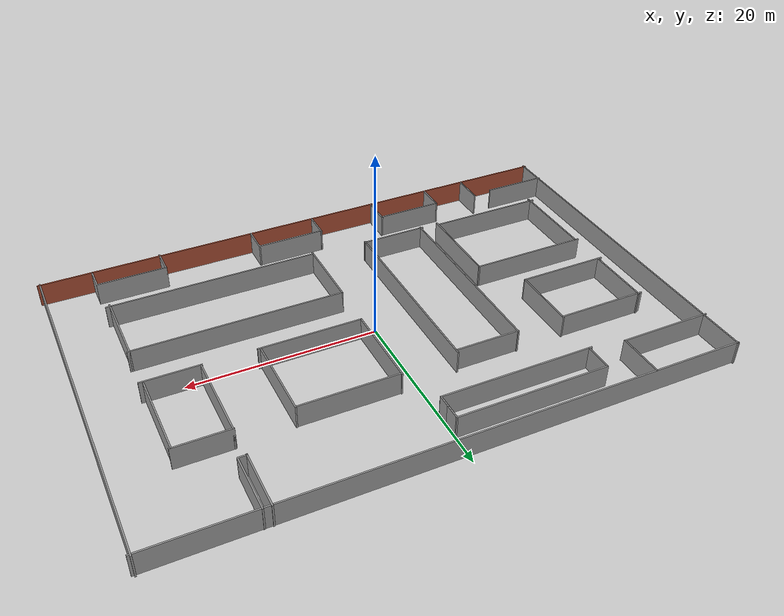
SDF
<?xml version='1.0'?>
<sdf version='1.7'>
  <model name='map_mir'>
    <link name='Wall_0'>
      <pose>0.059737 19.1491 0 0 -0 0</pose>
      <self_collide>0</self_collide>
      <enable_wind>0</enable_wind>
      <kinematic>0</kinematic>
      <visual name='Wall_0_Visual'>
        <pose>0 0 1.2475 0 -0 0</pose>
        <geometry>
          <box>
            <size>59.65 0.15 2.495</size>
          </box>
        </geometry>
        <material>
          <script>
            <uri>file://media/materials/scripts/gazebo.material</uri>
            <name>Gazebo/Grey</name>
          </script>
          <ambient>1 1 1 1</ambient>
          <shader type='pixel'/>
        </material>
        <meta>
          <layer>0</layer>
        </meta>
        <transparency>0</transparency>
        <cast_shadows>1</cast_shadows>
      </visual>
      <collision name='Wall_0_Collision'>
        <laser_retro>0</laser_retro>
        <max_contacts>10</max_contacts>
        <pose>0 0 1.2475 0 -0 0</pose>
        <geometry>
          <box>
            <size>59.65 0.15 2.495</size>
          </box>
        </geometry>
        <surface>
          <friction>
            <ode>
              <mu>1</mu>
              <mu2>1</mu2>
              <fdir1>0 0 0</fdir1>
              <slip1>0</slip1>
              <slip2>0</slip2>
            </ode>
            <torsional>
              <coefficient>1</coefficient>
              <patch_radius>0</patch_radius>
              <surface_radius>0</surface_radius>
              <use_patch_radius>1</use_patch_radius>
              <ode>
                <slip>0</slip>
              </ode>
            </torsional>
          </friction>
          <bounce>
            <restitution_coefficient>0</restitution_coefficient>
            <threshold>1e+06</threshold>
          </bounce>
          <contact>
            <collide_without_contact>0</collide_without_contact>
            <collide_without_contact_bitmask>1</collide_without_contact_bitmask>
            <collide_bitmask>1</collide_bitmask>
            <ode>
              <soft_cfm>0</soft_cfm>
              <soft_erp>0.2</soft_erp>
              <kp>1e+13</kp>
              <kd>1</kd>
              <max_vel>0.01</max_vel>
              <min_depth>0</min_depth>
            </ode>
            <bullet>
              <split_impulse>1</split_impulse>
              <split_impulse_penetration_threshold>-0.01</split_impulse_penetration_threshold>
              <soft_cfm>0</soft_cfm>
              <soft_erp>0.2</soft_erp>
              <kp>1e+13</kp>
              <kd>1</kd>
            </bullet>
          </contact>
        </surface>
      </collision>
    </link>
    <link name='Wall_1'>
      <pose>29.5673 0.013012 0 0 0 -1.5708</pose>
      <self_collide>0</self_collide>
      <enable_wind>0</enable_wind>
      <kinematic>0</kinematic>
      <visual name='Wall_1_Visual'>
        <pose>0 0 1.25 0 -0 0</pose>
        <geometry>
          <box>
            <size>38.75 0.15 2.5</size>
          </box>
        </geometry>
        <material>
          <script>
            <uri>file://media/materials/scripts/gazebo.material</uri>
            <name>Gazebo/Grey</name>
          </script>
          <ambient>1 1 1 1</ambient>
          <shader type='pixel'/>
        </material>
        <meta>
          <layer>0</layer>
        </meta>
        <transparency>0</transparency>
        <cast_shadows>1</cast_shadows>
      </visual>
      <collision name='Wall_1_Collision'>
        <laser_retro>0</laser_retro>
        <max_contacts>10</max_contacts>
        <pose>0 0 1.25 0 -0 0</pose>
        <geometry>
          <box>
            <size>38.75 0.15 2.5</size>
          </box>
        </geometry>
        <surface>
          <friction>
            <ode>
              <mu>1</mu>
              <mu2>1</mu2>
              <fdir1>0 0 0</fdir1>
              <slip1>0</slip1>
              <slip2>0</slip2>
            </ode>
            <torsional>
              <coefficient>1</coefficient>
              <patch_radius>0</patch_radius>
              <surface_radius>0</surface_radius>
              <use_patch_radius>1</use_patch_radius>
              <ode>
                <slip>0</slip>
              </ode>
            </torsional>
          </friction>
          <bounce>
            <restitution_coefficient>0</restitution_coefficient>
            <threshold>1e+06</threshold>
          </bounce>
          <contact>
            <collide_without_contact>0</collide_without_contact>
            <collide_without_contact_bitmask>1</collide_without_contact_bitmask>
            <collide_bitmask>1</collide_bitmask>
            <ode>
              <soft_cfm>0</soft_cfm>
              <soft_erp>0.2</soft_erp>
              <kp>1e+13</kp>
              <kd>1</kd>
              <max_vel>0.01</max_vel>
              <min_depth>0</min_depth>
            </ode>
            <bullet>
              <split_impulse>1</split_impulse>
              <split_impulse_penetration_threshold>-0.01</split_impulse_penetration_threshold>
              <soft_cfm>0</soft_cfm>
              <soft_erp>0.2</soft_erp>
              <kp>1e+13</kp>
              <kd>1</kd>
            </bullet>
          </contact>
        </surface>
      </collision>
    </link>
    <link name='Wall_2'>
      <pose>0.059738 -19.1013 0 0 -0 3.14159</pose>
      <self_collide>0</self_collide>
      <enable_wind>0</enable_wind>
      <kinematic>0</kinematic>
      <visual name='Wall_2_Visual'>
        <pose>0 0 1.25 0 -0 0</pose>
        <geometry>
          <box>
            <size>59.65 0.15 2.5</size>
          </box>
        </geometry>
        <material>
          <script>
            <uri>file://media/materials/scripts/gazebo.material</uri>
            <name>Gazebo/Bricks</name>
          </script>
          <ambient>1 0.764706 0.305882 1</ambient>
          <shader type='pixel'/>
        </material>
        <meta>
          <layer>0</layer>
        </meta>
        <transparency>0</transparency>
        <cast_shadows>1</cast_shadows>
      </visual>
      <collision name='Wall_2_Collision'>
        <laser_retro>0</laser_retro>
        <max_contacts>10</max_contacts>
        <pose>0 0 1.25 0 -0 0</pose>
        <geometry>
          <box>
            <size>59.65 0.15 2.5</size>
          </box>
        </geometry>
        <surface>
          <friction>
            <ode>
              <mu>1</mu>
              <mu2>1</mu2>
              <fdir1>0 0 0</fdir1>
              <slip1>0</slip1>
              <slip2>0</slip2>
            </ode>
            <torsional>
              <coefficient>1</coefficient>
              <patch_radius>0</patch_radius>
              <surface_radius>0</surface_radius>
              <use_patch_radius>1</use_patch_radius>
              <ode>
                <slip>0</slip>
              </ode>
            </torsional>
          </friction>
          <bounce>
            <restitution_coefficient>0</restitution_coefficient>
            <threshold>1e+06</threshold>
          </bounce>
          <contact>
            <collide_without_contact>0</collide_without_contact>
            <collide_without_contact_bitmask>1</collide_without_contact_bitmask>
            <collide_bitmask>1</collide_bitmask>
            <ode>
              <soft_cfm>0</soft_cfm>
              <soft_erp>0.2</soft_erp>
              <kp>1e+13</kp>
              <kd>1</kd>
              <max_vel>0.01</max_vel>
              <min_depth>0</min_depth>
            </ode>
            <bullet>
              <split_impulse>1</split_impulse>
              <split_impulse_penetration_threshold>-0.01</split_impulse_penetration_threshold>
              <soft_cfm>0</soft_cfm>
              <soft_erp>0.2</soft_erp>
              <kp>1e+13</kp>
              <kd>1</kd>
            </bullet>
          </contact>
        </surface>
      </collision>
    </link>
    <link name='Wall_25'>
      <pose>18.1409 16.1479 0 0 0 -1.5708</pose>
      <self_collide>0</self_collide>
      <enable_wind>0</enable_wind>
      <kinematic>0</kinematic>
      <visual name='Wall_25_Visual'>
        <pose>0 0 1.25 0 -0 0</pose>
        <geometry>
          <box>
            <size>6.32102 0.15 2.5</size>
          </box>
        </geometry>
        <material>
          <script>
            <uri>file://media/materials/scripts/gazebo.material</uri>
            <name>Gazebo/Grey</name>
          </script>
          <ambient>1 1 1 1</ambient>
          <shader type='pixel'/>
        </material>
        <meta>
          <layer>0</layer>
        </meta>
        <transparency>0</transparency>
        <cast_shadows>1</cast_shadows>
      </visual>
      <collision name='Wall_25_Collision'>
        <laser_retro>0</laser_retro>
        <max_contacts>10</max_contacts>
        <pose>0 0 1.25 0 -0 0</pose>
        <geometry>
          <box>
            <size>6.32102 0.15 2.5</size>
          </box>
        </geometry>
        <surface>
          <friction>
            <ode>
              <mu>1</mu>
              <mu2>1</mu2>
              <fdir1>0 0 0</fdir1>
              <slip1>0</slip1>
              <slip2>0</slip2>
            </ode>
            <torsional>
              <coefficient>1</coefficient>
              <patch_radius>0</patch_radius>
              <surface_radius>0</surface_radius>
              <use_patch_radius>1</use_patch_radius>
              <ode>
                <slip>0</slip>
              </ode>
            </torsional>
          </friction>
          <bounce>
            <restitution_coefficient>0</restitution_coefficient>
            <threshold>1e+06</threshold>
          </bounce>
          <contact>
            <collide_without_contact>0</collide_without_contact>
            <collide_without_contact_bitmask>1</collide_without_contact_bitmask>
            <collide_bitmask>1</collide_bitmask>
            <ode>
              <soft_cfm>0</soft_cfm>
              <soft_erp>0.2</soft_erp>
              <kp>1e+13</kp>
              <kd>1</kd>
              <max_vel>0.01</max_vel>
              <min_depth>0</min_depth>
            </ode>
            <bullet>
              <split_impulse>1</split_impulse>
              <split_impulse_penetration_threshold>-0.01</split_impulse_penetration_threshold>
              <soft_cfm>0</soft_cfm>
              <soft_erp>0.2</soft_erp>
              <kp>1e+13</kp>
              <kd>1</kd>
            </bullet>
          </contact>
        </surface>
      </collision>
    </link>
    <link name='Wall_26'>
      <pose>18.5514 13.1096 0 0 0 -0.015213</pose>
      <self_collide>0</self_collide>
      <enable_wind>0</enable_wind>
      <kinematic>0</kinematic>
      <visual name='Wall_26_Visual'>
        <pose>0 0 1.25 0 -0 0</pose>
        <geometry>
          <box>
            <size>0.971132 0.15 2.5</size>
          </box>
        </geometry>
        <material>
          <script>
            <uri>file://media/materials/scripts/gazebo.material</uri>
            <name>Gazebo/Grey</name>
          </script>
          <ambient>1 1 1 1</ambient>
          <shader type='pixel'/>
        </material>
        <meta>
          <layer>0</layer>
        </meta>
        <transparency>0</transparency>
        <cast_shadows>1</cast_shadows>
      </visual>
      <collision name='Wall_26_Collision'>
        <laser_retro>0</laser_retro>
        <max_contacts>10</max_contacts>
        <pose>0 0 1.25 0 -0 0</pose>
        <geometry>
          <box>
            <size>0.971132 0.15 2.5</size>
          </box>
        </geometry>
        <surface>
          <friction>
            <ode>
              <mu>1</mu>
              <mu2>1</mu2>
              <fdir1>0 0 0</fdir1>
              <slip1>0</slip1>
              <slip2>0</slip2>
            </ode>
            <torsional>
              <coefficient>1</coefficient>
              <patch_radius>0</patch_radius>
              <surface_radius>0</surface_radius>
              <use_patch_radius>1</use_patch_radius>
              <ode>
                <slip>0</slip>
              </ode>
            </torsional>
          </friction>
          <bounce>
            <restitution_coefficient>0</restitution_coefficient>
            <threshold>1e+06</threshold>
          </bounce>
          <contact>
            <collide_without_contact>0</collide_without_contact>
            <collide_without_contact_bitmask>1</collide_without_contact_bitmask>
            <collide_bitmask>1</collide_bitmask>
            <ode>
              <soft_cfm>0</soft_cfm>
              <soft_erp>0.2</soft_erp>
              <kp>1e+13</kp>
              <kd>1</kd>
              <max_vel>0.01</max_vel>
              <min_depth>0</min_depth>
            </ode>
            <bullet>
              <split_impulse>1</split_impulse>
              <split_impulse_penetration_threshold>-0.01</split_impulse_penetration_threshold>
              <soft_cfm>0</soft_cfm>
              <soft_erp>0.2</soft_erp>
              <kp>1e+13</kp>
              <kd>1</kd>
            </bullet>
          </contact>
        </surface>
      </collision>
    </link>
    <link name='Wall_27'>
      <pose>18.9619 16.1534 0 0 -0 1.5708</pose>
      <self_collide>0</self_collide>
      <enable_wind>0</enable_wind>
      <kinematic>0</kinematic>
      <visual name='Wall_27_Visual'>
        <pose>0 0 1.25 0 -0 0</pose>
        <geometry>
          <box>
            <size>6.25 0.15 2.5</size>
          </box>
        </geometry>
        <material>
          <script>
            <uri>file://media/materials/scripts/gazebo.material</uri>
            <name>Gazebo/Grey</name>
          </script>
          <ambient>1 1 1 1</ambient>
          <shader type='pixel'/>
        </material>
        <meta>
          <layer>0</layer>
        </meta>
        <transparency>0</transparency>
        <cast_shadows>1</cast_shadows>
      </visual>
      <collision name='Wall_27_Collision'>
        <laser_retro>0</laser_retro>
        <max_contacts>10</max_contacts>
        <pose>0 0 1.25 0 -0 0</pose>
        <geometry>
          <box>
            <size>6.25 0.15 2.5</size>
          </box>
        </geometry>
        <surface>
          <friction>
            <ode>
              <mu>1</mu>
              <mu2>1</mu2>
              <fdir1>0 0 0</fdir1>
              <slip1>0</slip1>
              <slip2>0</slip2>
            </ode>
            <torsional>
              <coefficient>1</coefficient>
              <patch_radius>0</patch_radius>
              <surface_radius>0</surface_radius>
              <use_patch_radius>1</use_patch_radius>
              <ode>
                <slip>0</slip>
              </ode>
            </torsional>
          </friction>
          <bounce>
            <restitution_coefficient>0</restitution_coefficient>
            <threshold>1e+06</threshold>
          </bounce>
          <contact>
            <collide_without_contact>0</collide_without_contact>
            <collide_without_contact_bitmask>1</collide_without_contact_bitmask>
            <collide_bitmask>1</collide_bitmask>
            <ode>
              <soft_cfm>0</soft_cfm>
              <soft_erp>0.2</soft_erp>
              <kp>1e+13</kp>
              <kd>1</kd>
              <max_vel>0.01</max_vel>
              <min_depth>0</min_depth>
            </ode>
            <bullet>
              <split_impulse>1</split_impulse>
              <split_impulse_penetration_threshold>-0.01</split_impulse_penetration_threshold>
              <soft_cfm>0</soft_cfm>
              <soft_erp>0.2</soft_erp>
              <kp>1e+13</kp>
              <kd>1</kd>
            </bullet>
          </contact>
        </surface>
      </collision>
    </link>
    <link name='Wall_29'>
      <pose>-26.2691 -15.9562 0 0 -0 0</pose>
      <self_collide>0</self_collide>
      <enable_wind>0</enable_wind>
      <kinematic>0</kinematic>
      <visual name='Wall_29_Visual'>
        <pose>0 0 1.25 0 -0 0</pose>
        <geometry>
          <box>
            <size>7 0.15 2.5</size>
          </box>
        </geometry>
        <material>
          <script>
            <uri>file://media/materials/scripts/gazebo.material</uri>
            <name>Gazebo/Grey</name>
          </script>
          <ambient>1 1 1 1</ambient>
          <shader type='pixel'/>
        </material>
        <meta>
          <layer>0</layer>
        </meta>
        <transparency>0</transparency>
        <cast_shadows>1</cast_shadows>
      </visual>
      <collision name='Wall_29_Collision'>
        <laser_retro>0</laser_retro>
        <max_contacts>10</max_contacts>
        <pose>0 0 1.25 0 -0 0</pose>
        <geometry>
          <box>
            <size>7 0.15 2.5</size>
          </box>
        </geometry>
        <surface>
          <friction>
            <ode>
              <mu>1</mu>
              <mu2>1</mu2>
              <fdir1>0 0 0</fdir1>
              <slip1>0</slip1>
              <slip2>0</slip2>
            </ode>
            <torsional>
              <coefficient>1</coefficient>
              <patch_radius>0</patch_radius>
              <surface_radius>0</surface_radius>
              <use_patch_radius>1</use_patch_radius>
              <ode>
                <slip>0</slip>
              </ode>
            </torsional>
          </friction>
          <bounce>
            <restitution_coefficient>0</restitution_coefficient>
            <threshold>1e+06</threshold>
          </bounce>
          <contact>
            <collide_without_contact>0</collide_without_contact>
            <collide_without_contact_bitmask>1</collide_without_contact_bitmask>
            <collide_bitmask>1</collide_bitmask>
            <ode>
              <soft_cfm>0</soft_cfm>
              <soft_erp>0.2</soft_erp>
              <kp>1e+13</kp>
              <kd>1</kd>
              <max_vel>0.01</max_vel>
              <min_depth>0</min_depth>
            </ode>
            <bullet>
              <split_impulse>1</split_impulse>
              <split_impulse_penetration_threshold>-0.01</split_impulse_penetration_threshold>
              <soft_cfm>0</soft_cfm>
              <soft_erp>0.2</soft_erp>
              <kp>1e+13</kp>
              <kd>1</kd>
            </bullet>
          </contact>
        </surface>
      </collision>
    </link>
    <link name='Wall_3'>
      <pose>-29.5785 0.001041 0 0 -0 1.5708</pose>
      <self_collide>0</self_collide>
      <enable_wind>0</enable_wind>
      <kinematic>0</kinematic>
      <visual name='Wall_3_Visual'>
        <pose>0 0 1.25 0 -0 0</pose>
        <geometry>
          <box>
            <size>38.75 0.15 2.5</size>
          </box>
        </geometry>
        <material>
          <script>
            <uri>file://media/materials/scripts/gazebo.material</uri>
            <name>Gazebo/Grey</name>
          </script>
          <ambient>1 1 1 1</ambient>
          <shader type='pixel'/>
        </material>
        <meta>
          <layer>0</layer>
        </meta>
        <transparency>0</transparency>
        <cast_shadows>1</cast_shadows>
      </visual>
      <collision name='Wall_3_Collision'>
        <laser_retro>0</laser_retro>
        <max_contacts>10</max_contacts>
        <pose>0 0 1.25 0 -0 0</pose>
        <geometry>
          <box>
            <size>38.75 0.15 2.5</size>
          </box>
        </geometry>
        <surface>
          <friction>
            <ode>
              <mu>1</mu>
              <mu2>1</mu2>
              <fdir1>0 0 0</fdir1>
              <slip1>0</slip1>
              <slip2>0</slip2>
            </ode>
            <torsional>
              <coefficient>1</coefficient>
              <patch_radius>0</patch_radius>
              <surface_radius>0</surface_radius>
              <use_patch_radius>1</use_patch_radius>
              <ode>
                <slip>0</slip>
              </ode>
            </torsional>
          </friction>
          <bounce>
            <restitution_coefficient>0</restitution_coefficient>
            <threshold>1e+06</threshold>
          </bounce>
          <contact>
            <collide_without_contact>0</collide_without_contact>
            <collide_without_contact_bitmask>1</collide_without_contact_bitmask>
            <collide_bitmask>1</collide_bitmask>
            <ode>
              <soft_cfm>0</soft_cfm>
              <soft_erp>0.2</soft_erp>
              <kp>1e+13</kp>
              <kd>1</kd>
              <max_vel>0.01</max_vel>
              <min_depth>0</min_depth>
            </ode>
            <bullet>
              <split_impulse>1</split_impulse>
              <split_impulse_penetration_threshold>-0.01</split_impulse_penetration_threshold>
              <soft_cfm>0</soft_cfm>
              <soft_erp>0.2</soft_erp>
              <kp>1e+13</kp>
              <kd>1</kd>
            </bullet>
          </contact>
        </surface>
      </collision>
    </link>
    <link name='Wall_31'>
      <pose>-20.4909 -17.3227 0 0 0 -1.5708</pose>
      <self_collide>0</self_collide>
      <enable_wind>0</enable_wind>
      <kinematic>0</kinematic>
      <visual name='Wall_31_Visual'>
        <pose>0 0 1.25 0 -0 0</pose>
        <geometry>
          <box>
            <size>3.5 0.15 2.5</size>
          </box>
        </geometry>
        <material>
          <script>
            <uri>file://media/materials/scripts/gazebo.material</uri>
            <name>Gazebo/Grey</name>
          </script>
          <ambient>1 1 1 1</ambient>
          <shader type='pixel'/>
        </material>
        <meta>
          <layer>0</layer>
        </meta>
        <transparency>0</transparency>
        <cast_shadows>1</cast_shadows>
      </visual>
      <collision name='Wall_31_Collision'>
        <laser_retro>0</laser_retro>
        <max_contacts>10</max_contacts>
        <pose>0 0 1.25 0 -0 0</pose>
        <geometry>
          <box>
            <size>3.5 0.15 2.5</size>
          </box>
        </geometry>
        <surface>
          <friction>
            <ode>
              <mu>1</mu>
              <mu2>1</mu2>
              <fdir1>0 0 0</fdir1>
              <slip1>0</slip1>
              <slip2>0</slip2>
            </ode>
            <torsional>
              <coefficient>1</coefficient>
              <patch_radius>0</patch_radius>
              <surface_radius>0</surface_radius>
              <use_patch_radius>1</use_patch_radius>
              <ode>
                <slip>0</slip>
              </ode>
            </torsional>
          </friction>
          <bounce>
            <restitution_coefficient>0</restitution_coefficient>
            <threshold>1e+06</threshold>
          </bounce>
          <contact>
            <collide_without_contact>0</collide_without_contact>
            <collide_without_contact_bitmask>1</collide_without_contact_bitmask>
            <collide_bitmask>1</collide_bitmask>
            <ode>
              <soft_cfm>0</soft_cfm>
              <soft_erp>0.2</soft_erp>
              <kp>1e+13</kp>
              <kd>1</kd>
              <max_vel>0.01</max_vel>
              <min_depth>0</min_depth>
            </ode>
            <bullet>
              <split_impulse>1</split_impulse>
              <split_impulse_penetration_threshold>-0.01</split_impulse_penetration_threshold>
              <soft_cfm>0</soft_cfm>
              <soft_erp>0.2</soft_erp>
              <kp>1e+13</kp>
              <kd>1</kd>
            </bullet>
          </contact>
        </surface>
      </collision>
    </link>
    <link name='Wall_34'>
      <pose>-15.5189 -17.5724 0 0 -0 1.5708</pose>
      <self_collide>0</self_collide>
      <enable_wind>0</enable_wind>
      <kinematic>0</kinematic>
      <visual name='Wall_34_Visual'>
        <pose>0 0 1.25 0 -0 0</pose>
        <geometry>
          <box>
            <size>3.25 0.15 2.5</size>
          </box>
        </geometry>
        <material>
          <script>
            <uri>file://media/materials/scripts/gazebo.material</uri>
            <name>Gazebo/Grey</name>
          </script>
          <ambient>1 1 1 1</ambient>
          <shader type='pixel'/>
        </material>
        <meta>
          <layer>0</layer>
        </meta>
        <transparency>0</transparency>
        <cast_shadows>1</cast_shadows>
      </visual>
      <collision name='Wall_34_Collision'>
        <laser_retro>0</laser_retro>
        <max_contacts>10</max_contacts>
        <pose>0 0 1.25 0 -0 0</pose>
        <geometry>
          <box>
            <size>3.25 0.15 2.5</size>
          </box>
        </geometry>
        <surface>
          <friction>
            <ode>
              <mu>1</mu>
              <mu2>1</mu2>
              <fdir1>0 0 0</fdir1>
              <slip1>0</slip1>
              <slip2>0</slip2>
            </ode>
            <torsional>
              <coefficient>1</coefficient>
              <patch_radius>0</patch_radius>
              <surface_radius>0</surface_radius>
              <use_patch_radius>1</use_patch_radius>
              <ode>
                <slip>0</slip>
              </ode>
            </torsional>
          </friction>
          <bounce>
            <restitution_coefficient>0</restitution_coefficient>
            <threshold>1e+06</threshold>
          </bounce>
          <contact>
            <collide_without_contact>0</collide_without_contact>
            <collide_without_contact_bitmask>1</collide_without_contact_bitmask>
            <collide_bitmask>1</collide_bitmask>
            <ode>
              <soft_cfm>0</soft_cfm>
              <soft_erp>0.2</soft_erp>
              <kp>1e+13</kp>
              <kd>1</kd>
              <max_vel>0.01</max_vel>
              <min_depth>0</min_depth>
            </ode>
            <bullet>
              <split_impulse>1</split_impulse>
              <split_impulse_penetration_threshold>-0.01</split_impulse_penetration_threshold>
              <soft_cfm>0</soft_cfm>
              <soft_erp>0.2</soft_erp>
              <kp>1e+13</kp>
              <kd>1</kd>
            </bullet>
          </contact>
        </surface>
      </collision>
    </link>
    <link name='Wall_35'>
      <pose>-11.9689 -16.0335 0 0 -0 0</pose>
      <self_collide>0</self_collide>
      <enable_wind>0</enable_wind>
      <kinematic>0</kinematic>
      <visual name='Wall_35_Visual'>
        <pose>0 0 1.25 0 -0 0</pose>
        <geometry>
          <box>
            <size>7.25 0.15 2.5</size>
          </box>
        </geometry>
        <material>
          <script>
            <uri>file://media/materials/scripts/gazebo.material</uri>
            <name>Gazebo/Grey</name>
          </script>
          <ambient>1 1 1 1</ambient>
          <shader type='pixel'/>
        </material>
        <meta>
          <layer>0</layer>
        </meta>
        <transparency>0</transparency>
        <cast_shadows>1</cast_shadows>
      </visual>
      <collision name='Wall_35_Collision'>
        <laser_retro>0</laser_retro>
        <max_contacts>10</max_contacts>
        <pose>0 0 1.25 0 -0 0</pose>
        <geometry>
          <box>
            <size>7.25 0.15 2.5</size>
          </box>
        </geometry>
        <surface>
          <friction>
            <ode>
              <mu>1</mu>
              <mu2>1</mu2>
              <fdir1>0 0 0</fdir1>
              <slip1>0</slip1>
              <slip2>0</slip2>
            </ode>
            <torsional>
              <coefficient>1</coefficient>
              <patch_radius>0</patch_radius>
              <surface_radius>0</surface_radius>
              <use_patch_radius>1</use_patch_radius>
              <ode>
                <slip>0</slip>
              </ode>
            </torsional>
          </friction>
          <bounce>
            <restitution_coefficient>0</restitution_coefficient>
            <threshold>1e+06</threshold>
          </bounce>
          <contact>
            <collide_without_contact>0</collide_without_contact>
            <collide_without_contact_bitmask>1</collide_without_contact_bitmask>
            <collide_bitmask>1</collide_bitmask>
            <ode>
              <soft_cfm>0</soft_cfm>
              <soft_erp>0.2</soft_erp>
              <kp>1e+13</kp>
              <kd>1</kd>
              <max_vel>0.01</max_vel>
              <min_depth>0</min_depth>
            </ode>
            <bullet>
              <split_impulse>1</split_impulse>
              <split_impulse_penetration_threshold>-0.01</split_impulse_penetration_threshold>
              <soft_cfm>0</soft_cfm>
              <soft_erp>0.2</soft_erp>
              <kp>1e+13</kp>
              <kd>1</kd>
            </bullet>
          </contact>
        </surface>
      </collision>
    </link>
    <link name='Wall_36'>
      <pose>-8.41885 -17.5112 0 0 0 -1.5708</pose>
      <self_collide>0</self_collide>
      <enable_wind>0</enable_wind>
      <kinematic>0</kinematic>
      <visual name='Wall_36_Visual'>
        <pose>0 0 1.25 0 -0 0</pose>
        <geometry>
          <box>
            <size>3.25 0.15 2.5</size>
          </box>
        </geometry>
        <material>
          <script>
            <uri>file://media/materials/scripts/gazebo.material</uri>
            <name>Gazebo/Grey</name>
          </script>
          <ambient>1 1 1 1</ambient>
          <shader type='pixel'/>
        </material>
        <meta>
          <layer>0</layer>
        </meta>
        <transparency>0</transparency>
        <cast_shadows>1</cast_shadows>
      </visual>
      <collision name='Wall_36_Collision'>
        <laser_retro>0</laser_retro>
        <max_contacts>10</max_contacts>
        <pose>0 0 1.25 0 -0 0</pose>
        <geometry>
          <box>
            <size>3.25 0.15 2.5</size>
          </box>
        </geometry>
        <surface>
          <friction>
            <ode>
              <mu>1</mu>
              <mu2>1</mu2>
              <fdir1>0 0 0</fdir1>
              <slip1>0</slip1>
              <slip2>0</slip2>
            </ode>
            <torsional>
              <coefficient>1</coefficient>
              <patch_radius>0</patch_radius>
              <surface_radius>0</surface_radius>
              <use_patch_radius>1</use_patch_radius>
              <ode>
                <slip>0</slip>
              </ode>
            </torsional>
          </friction>
          <bounce>
            <restitution_coefficient>0</restitution_coefficient>
            <threshold>1e+06</threshold>
          </bounce>
          <contact>
            <collide_without_contact>0</collide_without_contact>
            <collide_without_contact_bitmask>1</collide_without_contact_bitmask>
            <collide_bitmask>1</collide_bitmask>
            <ode>
              <soft_cfm>0</soft_cfm>
              <soft_erp>0.2</soft_erp>
              <kp>1e+13</kp>
              <kd>1</kd>
              <max_vel>0.01</max_vel>
              <min_depth>0</min_depth>
            </ode>
            <bullet>
              <split_impulse>1</split_impulse>
              <split_impulse_penetration_threshold>-0.01</split_impulse_penetration_threshold>
              <soft_cfm>0</soft_cfm>
              <soft_erp>0.2</soft_erp>
              <kp>1e+13</kp>
              <kd>1</kd>
            </bullet>
          </contact>
        </surface>
      </collision>
    </link>
    <link name='Wall_38'>
      <pose>-0.962038 -17.6768 0 0 -0 1.5708</pose>
      <self_collide>0</self_collide>
      <enable_wind>0</enable_wind>
      <kinematic>0</kinematic>
      <visual name='Wall_38_Visual'>
        <pose>0 0 1.25 0 -0 0</pose>
        <geometry>
          <box>
            <size>3 0.15 2.5</size>
          </box>
        </geometry>
        <material>
          <script>
            <uri>file://media/materials/scripts/gazebo.material</uri>
            <name>Gazebo/Grey</name>
          </script>
          <ambient>1 1 1 1</ambient>
          <shader type='pixel'/>
        </material>
        <meta>
          <layer>0</layer>
        </meta>
        <transparency>0</transparency>
        <cast_shadows>1</cast_shadows>
      </visual>
      <collision name='Wall_38_Collision'>
        <laser_retro>0</laser_retro>
        <max_contacts>10</max_contacts>
        <pose>0 0 1.25 0 -0 0</pose>
        <geometry>
          <box>
            <size>3 0.15 2.5</size>
          </box>
        </geometry>
        <surface>
          <friction>
            <ode>
              <mu>1</mu>
              <mu2>1</mu2>
              <fdir1>0 0 0</fdir1>
              <slip1>0</slip1>
              <slip2>0</slip2>
            </ode>
            <torsional>
              <coefficient>1</coefficient>
              <patch_radius>0</patch_radius>
              <surface_radius>0</surface_radius>
              <use_patch_radius>1</use_patch_radius>
              <ode>
                <slip>0</slip>
              </ode>
            </torsional>
          </friction>
          <bounce>
            <restitution_coefficient>0</restitution_coefficient>
            <threshold>1e+06</threshold>
          </bounce>
          <contact>
            <collide_without_contact>0</collide_without_contact>
            <collide_without_contact_bitmask>1</collide_without_contact_bitmask>
            <collide_bitmask>1</collide_bitmask>
            <ode>
              <soft_cfm>0</soft_cfm>
              <soft_erp>0.2</soft_erp>
              <kp>1e+13</kp>
              <kd>1</kd>
              <max_vel>0.01</max_vel>
              <min_depth>0</min_depth>
            </ode>
            <bullet>
              <split_impulse>1</split_impulse>
              <split_impulse_penetration_threshold>-0.01</split_impulse_penetration_threshold>
              <soft_cfm>0</soft_cfm>
              <soft_erp>0.2</soft_erp>
              <kp>1e+13</kp>
              <kd>1</kd>
            </bullet>
          </contact>
        </surface>
      </collision>
    </link>
    <link name='Wall_39'>
      <pose>2.71296 -16.3049 0 0 -0 0</pose>
      <self_collide>0</self_collide>
      <enable_wind>0</enable_wind>
      <kinematic>0</kinematic>
      <visual name='Wall_39_Visual'>
        <pose>0 0 1.25 0 -0 0</pose>
        <geometry>
          <box>
            <size>7.5 0.15 2.5</size>
          </box>
        </geometry>
        <material>
          <script>
            <uri>file://media/materials/scripts/gazebo.material</uri>
            <name>Gazebo/Grey</name>
          </script>
          <ambient>1 1 1 1</ambient>
          <shader type='pixel'/>
        </material>
        <meta>
          <layer>0</layer>
        </meta>
        <transparency>0</transparency>
        <cast_shadows>1</cast_shadows>
      </visual>
      <collision name='Wall_39_Collision'>
        <laser_retro>0</laser_retro>
        <max_contacts>10</max_contacts>
        <pose>0 0 1.25 0 -0 0</pose>
        <geometry>
          <box>
            <size>7.5 0.15 2.5</size>
          </box>
        </geometry>
        <surface>
          <friction>
            <ode>
              <mu>1</mu>
              <mu2>1</mu2>
              <fdir1>0 0 0</fdir1>
              <slip1>0</slip1>
              <slip2>0</slip2>
            </ode>
            <torsional>
              <coefficient>1</coefficient>
              <patch_radius>0</patch_radius>
              <surface_radius>0</surface_radius>
              <use_patch_radius>1</use_patch_radius>
              <ode>
                <slip>0</slip>
              </ode>
            </torsional>
          </friction>
          <bounce>
            <restitution_coefficient>0</restitution_coefficient>
            <threshold>1e+06</threshold>
          </bounce>
          <contact>
            <collide_without_contact>0</collide_without_contact>
            <collide_without_contact_bitmask>1</collide_without_contact_bitmask>
            <collide_bitmask>1</collide_bitmask>
            <ode>
              <soft_cfm>0</soft_cfm>
              <soft_erp>0.2</soft_erp>
              <kp>1e+13</kp>
              <kd>1</kd>
              <max_vel>0.01</max_vel>
              <min_depth>0</min_depth>
            </ode>
            <bullet>
              <split_impulse>1</split_impulse>
              <split_impulse_penetration_threshold>-0.01</split_impulse_penetration_threshold>
              <soft_cfm>0</soft_cfm>
              <soft_erp>0.2</soft_erp>
              <kp>1e+13</kp>
              <kd>1</kd>
            </bullet>
          </contact>
        </surface>
      </collision>
    </link>
    <link name='Wall_40'>
      <pose>6.38796 -17.6782 0 0 0 -1.5708</pose>
      <self_collide>0</self_collide>
      <enable_wind>0</enable_wind>
      <kinematic>0</kinematic>
      <visual name='Wall_40_Visual'>
        <pose>0 0 1.25 0 -0 0</pose>
        <geometry>
          <box>
            <size>3 0.15 2.5</size>
          </box>
        </geometry>
        <material>
          <script>
            <uri>file://media/materials/scripts/gazebo.material</uri>
            <name>Gazebo/Grey</name>
          </script>
          <ambient>1 1 1 1</ambient>
          <shader type='pixel'/>
        </material>
        <meta>
          <layer>0</layer>
        </meta>
        <transparency>0</transparency>
        <cast_shadows>1</cast_shadows>
      </visual>
      <collision name='Wall_40_Collision'>
        <laser_retro>0</laser_retro>
        <max_contacts>10</max_contacts>
        <pose>0 0 1.25 0 -0 0</pose>
        <geometry>
          <box>
            <size>3 0.15 2.5</size>
          </box>
        </geometry>
        <surface>
          <friction>
            <ode>
              <mu>1</mu>
              <mu2>1</mu2>
              <fdir1>0 0 0</fdir1>
              <slip1>0</slip1>
              <slip2>0</slip2>
            </ode>
            <torsional>
              <coefficient>1</coefficient>
              <patch_radius>0</patch_radius>
              <surface_radius>0</surface_radius>
              <use_patch_radius>1</use_patch_radius>
              <ode>
                <slip>0</slip>
              </ode>
            </torsional>
          </friction>
          <bounce>
            <restitution_coefficient>0</restitution_coefficient>
            <threshold>1e+06</threshold>
          </bounce>
          <contact>
            <collide_without_contact>0</collide_without_contact>
            <collide_without_contact_bitmask>1</collide_without_contact_bitmask>
            <collide_bitmask>1</collide_bitmask>
            <ode>
              <soft_cfm>0</soft_cfm>
              <soft_erp>0.2</soft_erp>
              <kp>1e+13</kp>
              <kd>1</kd>
              <max_vel>0.01</max_vel>
              <min_depth>0</min_depth>
            </ode>
            <bullet>
              <split_impulse>1</split_impulse>
              <split_impulse_penetration_threshold>-0.01</split_impulse_penetration_threshold>
              <soft_cfm>0</soft_cfm>
              <soft_erp>0.2</soft_erp>
              <kp>1e+13</kp>
              <kd>1</kd>
            </bullet>
          </contact>
        </surface>
      </collision>
    </link>
    <link name='Wall_42'>
      <pose>16.8174 -18.001 0 0 -0 1.5708</pose>
      <self_collide>0</self_collide>
      <enable_wind>0</enable_wind>
      <kinematic>0</kinematic>
      <visual name='Wall_42_Visual'>
        <pose>0 0 1.25 0 -0 0</pose>
        <geometry>
          <box>
            <size>2.75 0.15 2.5</size>
          </box>
        </geometry>
        <material>
          <script>
            <uri>file://media/materials/scripts/gazebo.material</uri>
            <name>Gazebo/Grey</name>
          </script>
          <ambient>1 1 1 1</ambient>
          <shader type='pixel'/>
        </material>
        <meta>
          <layer>0</layer>
        </meta>
        <transparency>0</transparency>
        <cast_shadows>1</cast_shadows>
      </visual>
      <collision name='Wall_42_Collision'>
        <laser_retro>0</laser_retro>
        <max_contacts>10</max_contacts>
        <pose>0 0 1.25 0 -0 0</pose>
        <geometry>
          <box>
            <size>2.75 0.15 2.5</size>
          </box>
        </geometry>
        <surface>
          <friction>
            <ode>
              <mu>1</mu>
              <mu2>1</mu2>
              <fdir1>0 0 0</fdir1>
              <slip1>0</slip1>
              <slip2>0</slip2>
            </ode>
            <torsional>
              <coefficient>1</coefficient>
              <patch_radius>0</patch_radius>
              <surface_radius>0</surface_radius>
              <use_patch_radius>1</use_patch_radius>
              <ode>
                <slip>0</slip>
              </ode>
            </torsional>
          </friction>
          <bounce>
            <restitution_coefficient>0</restitution_coefficient>
            <threshold>1e+06</threshold>
          </bounce>
          <contact>
            <collide_without_contact>0</collide_without_contact>
            <collide_without_contact_bitmask>1</collide_without_contact_bitmask>
            <collide_bitmask>1</collide_bitmask>
            <ode>
              <soft_cfm>0</soft_cfm>
              <soft_erp>0.2</soft_erp>
              <kp>1e+13</kp>
              <kd>1</kd>
              <max_vel>0.01</max_vel>
              <min_depth>0</min_depth>
            </ode>
            <bullet>
              <split_impulse>1</split_impulse>
              <split_impulse_penetration_threshold>-0.01</split_impulse_penetration_threshold>
              <soft_cfm>0</soft_cfm>
              <soft_erp>0.2</soft_erp>
              <kp>1e+13</kp>
              <kd>1</kd>
            </bullet>
          </contact>
        </surface>
      </collision>
    </link>
    <link name='Wall_43'>
      <pose>20.4924 -16.701 0 0 -0 0</pose>
      <self_collide>0</self_collide>
      <enable_wind>0</enable_wind>
      <kinematic>0</kinematic>
      <visual name='Wall_43_Visual'>
        <pose>0 0 1.25 0 -0 0</pose>
        <geometry>
          <box>
            <size>7.5 0.15 2.5</size>
          </box>
        </geometry>
        <material>
          <script>
            <uri>file://media/materials/scripts/gazebo.material</uri>
            <name>Gazebo/Grey</name>
          </script>
          <ambient>1 1 1 1</ambient>
          <shader type='pixel'/>
        </material>
        <meta>
          <layer>0</layer>
        </meta>
        <transparency>0</transparency>
        <cast_shadows>1</cast_shadows>
      </visual>
      <collision name='Wall_43_Collision'>
        <laser_retro>0</laser_retro>
        <max_contacts>10</max_contacts>
        <pose>0 0 1.25 0 -0 0</pose>
        <geometry>
          <box>
            <size>7.5 0.15 2.5</size>
          </box>
        </geometry>
        <surface>
          <friction>
            <ode>
              <mu>1</mu>
              <mu2>1</mu2>
              <fdir1>0 0 0</fdir1>
              <slip1>0</slip1>
              <slip2>0</slip2>
            </ode>
            <torsional>
              <coefficient>1</coefficient>
              <patch_radius>0</patch_radius>
              <surface_radius>0</surface_radius>
              <use_patch_radius>1</use_patch_radius>
              <ode>
                <slip>0</slip>
              </ode>
            </torsional>
          </friction>
          <bounce>
            <restitution_coefficient>0</restitution_coefficient>
            <threshold>1e+06</threshold>
          </bounce>
          <contact>
            <collide_without_contact>0</collide_without_contact>
            <collide_without_contact_bitmask>1</collide_without_contact_bitmask>
            <collide_bitmask>1</collide_bitmask>
            <ode>
              <soft_cfm>0</soft_cfm>
              <soft_erp>0.2</soft_erp>
              <kp>1e+13</kp>
              <kd>1</kd>
              <max_vel>0.01</max_vel>
              <min_depth>0</min_depth>
            </ode>
            <bullet>
              <split_impulse>1</split_impulse>
              <split_impulse_penetration_threshold>-0.01</split_impulse_penetration_threshold>
              <soft_cfm>0</soft_cfm>
              <soft_erp>0.2</soft_erp>
              <kp>1e+13</kp>
              <kd>1</kd>
            </bullet>
          </contact>
        </surface>
      </collision>
    </link>
    <link name='Wall_44'>
      <pose>24.1674 -17.876 0 0 0 -1.5708</pose>
      <self_collide>0</self_collide>
      <enable_wind>0</enable_wind>
      <kinematic>0</kinematic>
      <visual name='Wall_44_Visual'>
        <pose>0 0 1.25 0 -0 0</pose>
        <geometry>
          <box>
            <size>2.5 0.15 2.5</size>
          </box>
        </geometry>
        <material>
          <script>
            <uri>file://media/materials/scripts/gazebo.material</uri>
            <name>Gazebo/Grey</name>
          </script>
          <ambient>1 1 1 1</ambient>
          <shader type='pixel'/>
        </material>
        <meta>
          <layer>0</layer>
        </meta>
        <transparency>0</transparency>
        <cast_shadows>1</cast_shadows>
      </visual>
      <collision name='Wall_44_Collision'>
        <laser_retro>0</laser_retro>
        <max_contacts>10</max_contacts>
        <pose>0 0 1.25 0 -0 0</pose>
        <geometry>
          <box>
            <size>2.5 0.15 2.5</size>
          </box>
        </geometry>
        <surface>
          <friction>
            <ode>
              <mu>1</mu>
              <mu2>1</mu2>
              <fdir1>0 0 0</fdir1>
              <slip1>0</slip1>
              <slip2>0</slip2>
            </ode>
            <torsional>
              <coefficient>1</coefficient>
              <patch_radius>0</patch_radius>
              <surface_radius>0</surface_radius>
              <use_patch_radius>1</use_patch_radius>
              <ode>
                <slip>0</slip>
              </ode>
            </torsional>
          </friction>
          <bounce>
            <restitution_coefficient>0</restitution_coefficient>
            <threshold>1e+06</threshold>
          </bounce>
          <contact>
            <collide_without_contact>0</collide_without_contact>
            <collide_without_contact_bitmask>1</collide_without_contact_bitmask>
            <collide_bitmask>1</collide_bitmask>
            <ode>
              <soft_cfm>0</soft_cfm>
              <soft_erp>0.2</soft_erp>
              <kp>1e+13</kp>
              <kd>1</kd>
              <max_vel>0.01</max_vel>
              <min_depth>0</min_depth>
            </ode>
            <bullet>
              <split_impulse>1</split_impulse>
              <split_impulse_penetration_threshold>-0.01</split_impulse_penetration_threshold>
              <soft_cfm>0</soft_cfm>
              <soft_erp>0.2</soft_erp>
              <kp>1e+13</kp>
              <kd>1</kd>
            </bullet>
          </contact>
        </surface>
      </collision>
    </link>
    <link name='Wall_46'>
      <pose>12.91 -12.4029 0 0 -0 3.14159</pose>
      <self_collide>0</self_collide>
      <enable_wind>0</enable_wind>
      <kinematic>0</kinematic>
      <visual name='Wall_46_Visual'>
        <pose>0 0 1.25 0 -0 0</pose>
        <geometry>
          <box>
            <size>22.75 0.15 2.5</size>
          </box>
        </geometry>
        <material>
          <script>
            <uri>file://media/materials/scripts/gazebo.material</uri>
            <name>Gazebo/Grey</name>
          </script>
          <ambient>1 1 1 1</ambient>
          <shader type='pixel'/>
        </material>
        <meta>
          <layer>0</layer>
        </meta>
        <transparency>0</transparency>
        <cast_shadows>1</cast_shadows>
      </visual>
      <collision name='Wall_46_Collision'>
        <laser_retro>0</laser_retro>
        <max_contacts>10</max_contacts>
        <pose>0 0 1.25 0 -0 0</pose>
        <geometry>
          <box>
            <size>22.75 0.15 2.5</size>
          </box>
        </geometry>
        <surface>
          <friction>
            <ode>
              <mu>1</mu>
              <mu2>1</mu2>
              <fdir1>0 0 0</fdir1>
              <slip1>0</slip1>
              <slip2>0</slip2>
            </ode>
            <torsional>
              <coefficient>1</coefficient>
              <patch_radius>0</patch_radius>
              <surface_radius>0</surface_radius>
              <use_patch_radius>1</use_patch_radius>
              <ode>
                <slip>0</slip>
              </ode>
            </torsional>
          </friction>
          <bounce>
            <restitution_coefficient>0</restitution_coefficient>
            <threshold>1e+06</threshold>
          </bounce>
          <contact>
            <collide_without_contact>0</collide_without_contact>
            <collide_without_contact_bitmask>1</collide_without_contact_bitmask>
            <collide_bitmask>1</collide_bitmask>
            <ode>
              <soft_cfm>0</soft_cfm>
              <soft_erp>0.2</soft_erp>
              <kp>1e+13</kp>
              <kd>1</kd>
              <max_vel>0.01</max_vel>
              <min_depth>0</min_depth>
            </ode>
            <bullet>
              <split_impulse>1</split_impulse>
              <split_impulse_penetration_threshold>-0.01</split_impulse_penetration_threshold>
              <soft_cfm>0</soft_cfm>
              <soft_erp>0.2</soft_erp>
              <kp>1e+13</kp>
              <kd>1</kd>
            </bullet>
          </contact>
        </surface>
      </collision>
    </link>
    <link name='Wall_47'>
      <pose>1.60996 -8.60713 0 0 -0 1.5708</pose>
      <self_collide>0</self_collide>
      <enable_wind>0</enable_wind>
      <kinematic>0</kinematic>
      <visual name='Wall_47_Visual'>
        <pose>0 0 1.25 0 -0 0</pose>
        <geometry>
          <box>
            <size>8.25 0.15 2.5</size>
          </box>
        </geometry>
        <material>
          <script>
            <uri>file://media/materials/scripts/gazebo.material</uri>
            <name>Gazebo/Grey</name>
          </script>
          <ambient>1 1 1 1</ambient>
          <shader type='pixel'/>
        </material>
        <meta>
          <layer>0</layer>
        </meta>
        <transparency>0</transparency>
        <cast_shadows>1</cast_shadows>
      </visual>
      <collision name='Wall_47_Collision'>
        <laser_retro>0</laser_retro>
        <max_contacts>10</max_contacts>
        <pose>0 0 1.25 0 -0 0</pose>
        <geometry>
          <box>
            <size>8.25 0.15 2.5</size>
          </box>
        </geometry>
        <surface>
          <friction>
            <ode>
              <mu>1</mu>
              <mu2>1</mu2>
              <fdir1>0 0 0</fdir1>
              <slip1>0</slip1>
              <slip2>0</slip2>
            </ode>
            <torsional>
              <coefficient>1</coefficient>
              <patch_radius>0</patch_radius>
              <surface_radius>0</surface_radius>
              <use_patch_radius>1</use_patch_radius>
              <ode>
                <slip>0</slip>
              </ode>
            </torsional>
          </friction>
          <bounce>
            <restitution_coefficient>0</restitution_coefficient>
            <threshold>1e+06</threshold>
          </bounce>
          <contact>
            <collide_without_contact>0</collide_without_contact>
            <collide_without_contact_bitmask>1</collide_without_contact_bitmask>
            <collide_bitmask>1</collide_bitmask>
            <ode>
              <soft_cfm>0</soft_cfm>
              <soft_erp>0.2</soft_erp>
              <kp>1e+13</kp>
              <kd>1</kd>
              <max_vel>0.01</max_vel>
              <min_depth>0</min_depth>
            </ode>
            <bullet>
              <split_impulse>1</split_impulse>
              <split_impulse_penetration_threshold>-0.01</split_impulse_penetration_threshold>
              <soft_cfm>0</soft_cfm>
              <soft_erp>0.2</soft_erp>
              <kp>1e+13</kp>
              <kd>1</kd>
            </bullet>
          </contact>
        </surface>
      </collision>
    </link>
    <link name='Wall_48'>
      <pose>12.785 -4.55713 0 0 -0 0</pose>
      <self_collide>0</self_collide>
      <enable_wind>0</enable_wind>
      <kinematic>0</kinematic>
      <visual name='Wall_48_Visual'>
        <pose>0 0 1.25 0 -0 0</pose>
        <geometry>
          <box>
            <size>22.5 0.15 2.5</size>
          </box>
        </geometry>
        <material>
          <script>
            <uri>file://media/materials/scripts/gazebo.material</uri>
            <name>Gazebo/Grey</name>
          </script>
          <ambient>1 1 1 1</ambient>
          <shader type='pixel'/>
        </material>
        <meta>
          <layer>0</layer>
        </meta>
        <transparency>0</transparency>
        <cast_shadows>1</cast_shadows>
      </visual>
      <collision name='Wall_48_Collision'>
        <laser_retro>0</laser_retro>
        <max_contacts>10</max_contacts>
        <pose>0 0 1.25 0 -0 0</pose>
        <geometry>
          <box>
            <size>22.5 0.15 2.5</size>
          </box>
        </geometry>
        <surface>
          <friction>
            <ode>
              <mu>1</mu>
              <mu2>1</mu2>
              <fdir1>0 0 0</fdir1>
              <slip1>0</slip1>
              <slip2>0</slip2>
            </ode>
            <torsional>
              <coefficient>1</coefficient>
              <patch_radius>0</patch_radius>
              <surface_radius>0</surface_radius>
              <use_patch_radius>1</use_patch_radius>
              <ode>
                <slip>0</slip>
              </ode>
            </torsional>
          </friction>
          <bounce>
            <restitution_coefficient>0</restitution_coefficient>
            <threshold>1e+06</threshold>
          </bounce>
          <contact>
            <collide_without_contact>0</collide_without_contact>
            <collide_without_contact_bitmask>1</collide_without_contact_bitmask>
            <collide_bitmask>1</collide_bitmask>
            <ode>
              <soft_cfm>0</soft_cfm>
              <soft_erp>0.2</soft_erp>
              <kp>1e+13</kp>
              <kd>1</kd>
              <max_vel>0.01</max_vel>
              <min_depth>0</min_depth>
            </ode>
            <bullet>
              <split_impulse>1</split_impulse>
              <split_impulse_penetration_threshold>-0.01</split_impulse_penetration_threshold>
              <soft_cfm>0</soft_cfm>
              <soft_erp>0.2</soft_erp>
              <kp>1e+13</kp>
              <kd>1</kd>
            </bullet>
          </contact>
        </surface>
      </collision>
    </link>
    <link name='Wall_49'>
      <pose>23.785 -8.60713 0 0 0 -1.5708</pose>
      <self_collide>0</self_collide>
      <enable_wind>0</enable_wind>
      <kinematic>0</kinematic>
      <visual name='Wall_49_Visual'>
        <pose>0 0 1.25 0 -0 0</pose>
        <geometry>
          <box>
            <size>8.25 0.15 2.5</size>
          </box>
        </geometry>
        <material>
          <script>
            <uri>file://media/materials/scripts/gazebo.material</uri>
            <name>Gazebo/Grey</name>
          </script>
          <ambient>1 1 1 1</ambient>
          <shader type='pixel'/>
        </material>
        <meta>
          <layer>0</layer>
        </meta>
        <transparency>0</transparency>
        <cast_shadows>1</cast_shadows>
      </visual>
      <collision name='Wall_49_Collision'>
        <laser_retro>0</laser_retro>
        <max_contacts>10</max_contacts>
        <pose>0 0 1.25 0 -0 0</pose>
        <geometry>
          <box>
            <size>8.25 0.15 2.5</size>
          </box>
        </geometry>
        <surface>
          <friction>
            <ode>
              <mu>1</mu>
              <mu2>1</mu2>
              <fdir1>0 0 0</fdir1>
              <slip1>0</slip1>
              <slip2>0</slip2>
            </ode>
            <torsional>
              <coefficient>1</coefficient>
              <patch_radius>0</patch_radius>
              <surface_radius>0</surface_radius>
              <use_patch_radius>1</use_patch_radius>
              <ode>
                <slip>0</slip>
              </ode>
            </torsional>
          </friction>
          <bounce>
            <restitution_coefficient>0</restitution_coefficient>
            <threshold>1e+06</threshold>
          </bounce>
          <contact>
            <collide_without_contact>0</collide_without_contact>
            <collide_without_contact_bitmask>1</collide_without_contact_bitmask>
            <collide_bitmask>1</collide_bitmask>
            <ode>
              <soft_cfm>0</soft_cfm>
              <soft_erp>0.2</soft_erp>
              <kp>1e+13</kp>
              <kd>1</kd>
              <max_vel>0.01</max_vel>
              <min_depth>0</min_depth>
            </ode>
            <bullet>
              <split_impulse>1</split_impulse>
              <split_impulse_penetration_threshold>-0.01</split_impulse_penetration_threshold>
              <soft_cfm>0</soft_cfm>
              <soft_erp>0.2</soft_erp>
              <kp>1e+13</kp>
              <kd>1</kd>
            </bullet>
          </contact>
        </surface>
      </collision>
    </link>
    <link name='Wall_51'>
      <pose>21.1138 0.256385 0 0 -0 3.14159</pose>
      <self_collide>0</self_collide>
      <enable_wind>0</enable_wind>
      <kinematic>0</kinematic>
      <visual name='Wall_51_Visual'>
        <pose>0 0 1.25 0 -0 0</pose>
        <geometry>
          <box>
            <size>6.15512 0.15 2.5</size>
          </box>
        </geometry>
        <material>
          <script>
            <uri>file://media/materials/scripts/gazebo.material</uri>
            <name>Gazebo/Grey</name>
          </script>
          <ambient>1 1 1 1</ambient>
          <shader type='pixel'/>
        </material>
        <meta>
          <layer>0</layer>
        </meta>
        <transparency>0</transparency>
        <cast_shadows>1</cast_shadows>
      </visual>
      <collision name='Wall_51_Collision'>
        <laser_retro>0</laser_retro>
        <max_contacts>10</max_contacts>
        <pose>0 0 1.25 0 -0 0</pose>
        <geometry>
          <box>
            <size>6.15512 0.15 2.5</size>
          </box>
        </geometry>
        <surface>
          <friction>
            <ode>
              <mu>1</mu>
              <mu2>1</mu2>
              <fdir1>0 0 0</fdir1>
              <slip1>0</slip1>
              <slip2>0</slip2>
            </ode>
            <torsional>
              <coefficient>1</coefficient>
              <patch_radius>0</patch_radius>
              <surface_radius>0</surface_radius>
              <use_patch_radius>1</use_patch_radius>
              <ode>
                <slip>0</slip>
              </ode>
            </torsional>
          </friction>
          <bounce>
            <restitution_coefficient>0</restitution_coefficient>
            <threshold>1e+06</threshold>
          </bounce>
          <contact>
            <collide_without_contact>0</collide_without_contact>
            <collide_without_contact_bitmask>1</collide_without_contact_bitmask>
            <collide_bitmask>1</collide_bitmask>
            <ode>
              <soft_cfm>0</soft_cfm>
              <soft_erp>0.2</soft_erp>
              <kp>1e+13</kp>
              <kd>1</kd>
              <max_vel>0.01</max_vel>
              <min_depth>0</min_depth>
            </ode>
            <bullet>
              <split_impulse>1</split_impulse>
              <split_impulse_penetration_threshold>-0.01</split_impulse_penetration_threshold>
              <soft_cfm>0</soft_cfm>
              <soft_erp>0.2</soft_erp>
              <kp>1e+13</kp>
              <kd>1</kd>
            </bullet>
          </contact>
        </surface>
      </collision>
    </link>
    <link name='Wall_52'>
      <pose>18.182 4.93138 0 0 -0 1.5708</pose>
      <self_collide>0</self_collide>
      <enable_wind>0</enable_wind>
      <kinematic>0</kinematic>
      <visual name='Wall_52_Visual'>
        <pose>0 0 1.25 0 -0 0</pose>
        <geometry>
          <box>
            <size>9.5 0.15 2.5</size>
          </box>
        </geometry>
        <material>
          <script>
            <uri>file://media/materials/scripts/gazebo.material</uri>
            <name>Gazebo/Grey</name>
          </script>
          <ambient>1 1 1 1</ambient>
          <shader type='pixel'/>
        </material>
        <meta>
          <layer>0</layer>
        </meta>
        <transparency>0</transparency>
        <cast_shadows>1</cast_shadows>
      </visual>
      <collision name='Wall_52_Collision'>
        <laser_retro>0</laser_retro>
        <max_contacts>10</max_contacts>
        <pose>0 0 1.25 0 -0 0</pose>
        <geometry>
          <box>
            <size>9.5 0.15 2.5</size>
          </box>
        </geometry>
        <surface>
          <friction>
            <ode>
              <mu>1</mu>
              <mu2>1</mu2>
              <fdir1>0 0 0</fdir1>
              <slip1>0</slip1>
              <slip2>0</slip2>
            </ode>
            <torsional>
              <coefficient>1</coefficient>
              <patch_radius>0</patch_radius>
              <surface_radius>0</surface_radius>
              <use_patch_radius>1</use_patch_radius>
              <ode>
                <slip>0</slip>
              </ode>
            </torsional>
          </friction>
          <bounce>
            <restitution_coefficient>0</restitution_coefficient>
            <threshold>1e+06</threshold>
          </bounce>
          <contact>
            <collide_without_contact>0</collide_without_contact>
            <collide_without_contact_bitmask>1</collide_without_contact_bitmask>
            <collide_bitmask>1</collide_bitmask>
            <ode>
              <soft_cfm>0</soft_cfm>
              <soft_erp>0.2</soft_erp>
              <kp>1e+13</kp>
              <kd>1</kd>
              <max_vel>0.01</max_vel>
              <min_depth>0</min_depth>
            </ode>
            <bullet>
              <split_impulse>1</split_impulse>
              <split_impulse_penetration_threshold>-0.01</split_impulse_penetration_threshold>
              <soft_cfm>0</soft_cfm>
              <soft_erp>0.2</soft_erp>
              <kp>1e+13</kp>
              <kd>1</kd>
            </bullet>
          </contact>
        </surface>
      </collision>
    </link>
    <link name='Wall_53'>
      <pose>20.9888 9.60638 0 0 -0 0</pose>
      <self_collide>0</self_collide>
      <enable_wind>0</enable_wind>
      <kinematic>0</kinematic>
      <visual name='Wall_53_Visual'>
        <pose>0 0 1.25 0 -0 0</pose>
        <geometry>
          <box>
            <size>5.90512 0.15 2.5</size>
          </box>
        </geometry>
        <material>
          <script>
            <uri>file://media/materials/scripts/gazebo.material</uri>
            <name>Gazebo/Grey</name>
          </script>
          <ambient>1 1 1 1</ambient>
          <shader type='pixel'/>
        </material>
        <meta>
          <layer>0</layer>
        </meta>
        <transparency>0</transparency>
        <cast_shadows>1</cast_shadows>
      </visual>
      <collision name='Wall_53_Collision'>
        <laser_retro>0</laser_retro>
        <max_contacts>10</max_contacts>
        <pose>0 0 1.25 0 -0 0</pose>
        <geometry>
          <box>
            <size>5.90512 0.15 2.5</size>
          </box>
        </geometry>
        <surface>
          <friction>
            <ode>
              <mu>1</mu>
              <mu2>1</mu2>
              <fdir1>0 0 0</fdir1>
              <slip1>0</slip1>
              <slip2>0</slip2>
            </ode>
            <torsional>
              <coefficient>1</coefficient>
              <patch_radius>0</patch_radius>
              <surface_radius>0</surface_radius>
              <use_patch_radius>1</use_patch_radius>
              <ode>
                <slip>0</slip>
              </ode>
            </torsional>
          </friction>
          <bounce>
            <restitution_coefficient>0</restitution_coefficient>
            <threshold>1e+06</threshold>
          </bounce>
          <contact>
            <collide_without_contact>0</collide_without_contact>
            <collide_without_contact_bitmask>1</collide_without_contact_bitmask>
            <collide_bitmask>1</collide_bitmask>
            <ode>
              <soft_cfm>0</soft_cfm>
              <soft_erp>0.2</soft_erp>
              <kp>1e+13</kp>
              <kd>1</kd>
              <max_vel>0.01</max_vel>
              <min_depth>0</min_depth>
            </ode>
            <bullet>
              <split_impulse>1</split_impulse>
              <split_impulse_penetration_threshold>-0.01</split_impulse_penetration_threshold>
              <soft_cfm>0</soft_cfm>
              <soft_erp>0.2</soft_erp>
              <kp>1e+13</kp>
              <kd>1</kd>
            </bullet>
          </contact>
        </surface>
      </collision>
    </link>
    <link name='Wall_54'>
      <pose>23.72 5.05638 0 0 0 -1.5708</pose>
      <self_collide>0</self_collide>
      <enable_wind>0</enable_wind>
      <kinematic>0</kinematic>
      <visual name='Wall_54_Visual'>
        <pose>0 0 1.25 0 -0 0</pose>
        <geometry>
          <box>
            <size>9.25 0.15 2.5</size>
          </box>
        </geometry>
        <material>
          <script>
            <uri>file://media/materials/scripts/gazebo.material</uri>
            <name>Gazebo/Grey</name>
          </script>
          <ambient>1 1 1 1</ambient>
          <shader type='pixel'/>
        </material>
        <meta>
          <layer>0</layer>
        </meta>
        <transparency>0</transparency>
        <cast_shadows>1</cast_shadows>
      </visual>
      <collision name='Wall_54_Collision'>
        <laser_retro>0</laser_retro>
        <max_contacts>10</max_contacts>
        <pose>0 0 1.25 0 -0 0</pose>
        <geometry>
          <box>
            <size>9.25 0.15 2.5</size>
          </box>
        </geometry>
        <surface>
          <friction>
            <ode>
              <mu>1</mu>
              <mu2>1</mu2>
              <fdir1>0 0 0</fdir1>
              <slip1>0</slip1>
              <slip2>0</slip2>
            </ode>
            <torsional>
              <coefficient>1</coefficient>
              <patch_radius>0</patch_radius>
              <surface_radius>0</surface_radius>
              <use_patch_radius>1</use_patch_radius>
              <ode>
                <slip>0</slip>
              </ode>
            </torsional>
          </friction>
          <bounce>
            <restitution_coefficient>0</restitution_coefficient>
            <threshold>1e+06</threshold>
          </bounce>
          <contact>
            <collide_without_contact>0</collide_without_contact>
            <collide_without_contact_bitmask>1</collide_without_contact_bitmask>
            <collide_bitmask>1</collide_bitmask>
            <ode>
              <soft_cfm>0</soft_cfm>
              <soft_erp>0.2</soft_erp>
              <kp>1e+13</kp>
              <kd>1</kd>
              <max_vel>0.01</max_vel>
              <min_depth>0</min_depth>
            </ode>
            <bullet>
              <split_impulse>1</split_impulse>
              <split_impulse_penetration_threshold>-0.01</split_impulse_penetration_threshold>
              <soft_cfm>0</soft_cfm>
              <soft_erp>0.2</soft_erp>
              <kp>1e+13</kp>
              <kd>1</kd>
            </bullet>
          </contact>
        </surface>
      </collision>
    </link>
    <link name='Wall_56'>
      <pose>7.123 0.333271 0 0 -0 3.14159</pose>
      <self_collide>0</self_collide>
      <enable_wind>0</enable_wind>
      <kinematic>0</kinematic>
      <visual name='Wall_56_Visual'>
        <pose>0 0 1.25 0 -0 0</pose>
        <geometry>
          <box>
            <size>11 0.15 2.5</size>
          </box>
        </geometry>
        <material>
          <script>
            <uri>file://media/materials/scripts/gazebo.material</uri>
            <name>Gazebo/Grey</name>
          </script>
          <ambient>1 1 1 1</ambient>
          <shader type='pixel'/>
        </material>
        <meta>
          <layer>0</layer>
        </meta>
        <transparency>0</transparency>
        <cast_shadows>1</cast_shadows>
      </visual>
      <collision name='Wall_56_Collision'>
        <laser_retro>0</laser_retro>
        <max_contacts>10</max_contacts>
        <pose>0 0 1.25 0 -0 0</pose>
        <geometry>
          <box>
            <size>11 0.15 2.5</size>
          </box>
        </geometry>
        <surface>
          <friction>
            <ode>
              <mu>1</mu>
              <mu2>1</mu2>
              <fdir1>0 0 0</fdir1>
              <slip1>0</slip1>
              <slip2>0</slip2>
            </ode>
            <torsional>
              <coefficient>1</coefficient>
              <patch_radius>0</patch_radius>
              <surface_radius>0</surface_radius>
              <use_patch_radius>1</use_patch_radius>
              <ode>
                <slip>0</slip>
              </ode>
            </torsional>
          </friction>
          <bounce>
            <restitution_coefficient>0</restitution_coefficient>
            <threshold>1e+06</threshold>
          </bounce>
          <contact>
            <collide_without_contact>0</collide_without_contact>
            <collide_without_contact_bitmask>1</collide_without_contact_bitmask>
            <collide_bitmask>1</collide_bitmask>
            <ode>
              <soft_cfm>0</soft_cfm>
              <soft_erp>0.2</soft_erp>
              <kp>1e+13</kp>
              <kd>1</kd>
              <max_vel>0.01</max_vel>
              <min_depth>0</min_depth>
            </ode>
            <bullet>
              <split_impulse>1</split_impulse>
              <split_impulse_penetration_threshold>-0.01</split_impulse_penetration_threshold>
              <soft_cfm>0</soft_cfm>
              <soft_erp>0.2</soft_erp>
              <kp>1e+13</kp>
              <kd>1</kd>
            </bullet>
          </contact>
        </surface>
      </collision>
    </link>
    <link name='Wall_57'>
      <pose>1.698 4.88327 0 0 -0 1.5708</pose>
      <self_collide>0</self_collide>
      <enable_wind>0</enable_wind>
      <kinematic>0</kinematic>
      <visual name='Wall_57_Visual'>
        <pose>0 0 1.25 0 -0 0</pose>
        <geometry>
          <box>
            <size>9.25 0.15 2.5</size>
          </box>
        </geometry>
        <material>
          <script>
            <uri>file://media/materials/scripts/gazebo.material</uri>
            <name>Gazebo/Grey</name>
          </script>
          <ambient>1 1 1 1</ambient>
          <shader type='pixel'/>
        </material>
        <meta>
          <layer>0</layer>
        </meta>
        <transparency>0</transparency>
        <cast_shadows>1</cast_shadows>
      </visual>
      <collision name='Wall_57_Collision'>
        <laser_retro>0</laser_retro>
        <max_contacts>10</max_contacts>
        <pose>0 0 1.25 0 -0 0</pose>
        <geometry>
          <box>
            <size>9.25 0.15 2.5</size>
          </box>
        </geometry>
        <surface>
          <friction>
            <ode>
              <mu>1</mu>
              <mu2>1</mu2>
              <fdir1>0 0 0</fdir1>
              <slip1>0</slip1>
              <slip2>0</slip2>
            </ode>
            <torsional>
              <coefficient>1</coefficient>
              <patch_radius>0</patch_radius>
              <surface_radius>0</surface_radius>
              <use_patch_radius>1</use_patch_radius>
              <ode>
                <slip>0</slip>
              </ode>
            </torsional>
          </friction>
          <bounce>
            <restitution_coefficient>0</restitution_coefficient>
            <threshold>1e+06</threshold>
          </bounce>
          <contact>
            <collide_without_contact>0</collide_without_contact>
            <collide_without_contact_bitmask>1</collide_without_contact_bitmask>
            <collide_bitmask>1</collide_bitmask>
            <ode>
              <soft_cfm>0</soft_cfm>
              <soft_erp>0.2</soft_erp>
              <kp>1e+13</kp>
              <kd>1</kd>
              <max_vel>0.01</max_vel>
              <min_depth>0</min_depth>
            </ode>
            <bullet>
              <split_impulse>1</split_impulse>
              <split_impulse_penetration_threshold>-0.01</split_impulse_penetration_threshold>
              <soft_cfm>0</soft_cfm>
              <soft_erp>0.2</soft_erp>
              <kp>1e+13</kp>
              <kd>1</kd>
            </bullet>
          </contact>
        </surface>
      </collision>
    </link>
    <link name='Wall_58'>
      <pose>6.998 9.35526 0 0 -0 0</pose>
      <self_collide>0</self_collide>
      <enable_wind>0</enable_wind>
      <kinematic>0</kinematic>
      <visual name='Wall_58_Visual'>
        <pose>0 0 1.25 0 -0 0</pose>
        <geometry>
          <box>
            <size>10.75 0.15 2.5</size>
          </box>
        </geometry>
        <material>
          <script>
            <uri>file://media/materials/scripts/gazebo.material</uri>
            <name>Gazebo/Grey</name>
          </script>
          <ambient>1 1 1 1</ambient>
          <shader type='pixel'/>
        </material>
        <meta>
          <layer>0</layer>
        </meta>
        <transparency>0</transparency>
        <cast_shadows>1</cast_shadows>
      </visual>
      <collision name='Wall_58_Collision'>
        <laser_retro>0</laser_retro>
        <max_contacts>10</max_contacts>
        <pose>0 0 1.25 0 -0 0</pose>
        <geometry>
          <box>
            <size>10.75 0.15 2.5</size>
          </box>
        </geometry>
        <surface>
          <friction>
            <ode>
              <mu>1</mu>
              <mu2>1</mu2>
              <fdir1>0 0 0</fdir1>
              <slip1>0</slip1>
              <slip2>0</slip2>
            </ode>
            <torsional>
              <coefficient>1</coefficient>
              <patch_radius>0</patch_radius>
              <surface_radius>0</surface_radius>
              <use_patch_radius>1</use_patch_radius>
              <ode>
                <slip>0</slip>
              </ode>
            </torsional>
          </friction>
          <bounce>
            <restitution_coefficient>0</restitution_coefficient>
            <threshold>1e+06</threshold>
          </bounce>
          <contact>
            <collide_without_contact>0</collide_without_contact>
            <collide_without_contact_bitmask>1</collide_without_contact_bitmask>
            <collide_bitmask>1</collide_bitmask>
            <ode>
              <soft_cfm>0</soft_cfm>
              <soft_erp>0.2</soft_erp>
              <kp>1e+13</kp>
              <kd>1</kd>
              <max_vel>0.01</max_vel>
              <min_depth>0</min_depth>
            </ode>
            <bullet>
              <split_impulse>1</split_impulse>
              <split_impulse_penetration_threshold>-0.01</split_impulse_penetration_threshold>
              <soft_cfm>0</soft_cfm>
              <soft_erp>0.2</soft_erp>
              <kp>1e+13</kp>
              <kd>1</kd>
            </bullet>
          </contact>
        </surface>
      </collision>
    </link>
    <link name='Wall_59'>
      <pose>12.298 4.88327 0 0 0 -1.5708</pose>
      <self_collide>0</self_collide>
      <enable_wind>0</enable_wind>
      <kinematic>0</kinematic>
      <visual name='Wall_59_Visual'>
        <pose>0 0 1.25 0 -0 0</pose>
        <geometry>
          <box>
            <size>9.25 0.15 2.5</size>
          </box>
        </geometry>
        <material>
          <script>
            <uri>file://media/materials/scripts/gazebo.material</uri>
            <name>Gazebo/Grey</name>
          </script>
          <ambient>1 1 1 1</ambient>
          <shader type='pixel'/>
        </material>
        <meta>
          <layer>0</layer>
        </meta>
        <transparency>0</transparency>
        <cast_shadows>1</cast_shadows>
      </visual>
      <collision name='Wall_59_Collision'>
        <laser_retro>0</laser_retro>
        <max_contacts>10</max_contacts>
        <pose>0 0 1.25 0 -0 0</pose>
        <geometry>
          <box>
            <size>9.25 0.15 2.5</size>
          </box>
        </geometry>
        <surface>
          <friction>
            <ode>
              <mu>1</mu>
              <mu2>1</mu2>
              <fdir1>0 0 0</fdir1>
              <slip1>0</slip1>
              <slip2>0</slip2>
            </ode>
            <torsional>
              <coefficient>1</coefficient>
              <patch_radius>0</patch_radius>
              <surface_radius>0</surface_radius>
              <use_patch_radius>1</use_patch_radius>
              <ode>
                <slip>0</slip>
              </ode>
            </torsional>
          </friction>
          <bounce>
            <restitution_coefficient>0</restitution_coefficient>
            <threshold>1e+06</threshold>
          </bounce>
          <contact>
            <collide_without_contact>0</collide_without_contact>
            <collide_without_contact_bitmask>1</collide_without_contact_bitmask>
            <collide_bitmask>1</collide_bitmask>
            <ode>
              <soft_cfm>0</soft_cfm>
              <soft_erp>0.2</soft_erp>
              <kp>1e+13</kp>
              <kd>1</kd>
              <max_vel>0.01</max_vel>
              <min_depth>0</min_depth>
            </ode>
            <bullet>
              <split_impulse>1</split_impulse>
              <split_impulse_penetration_threshold>-0.01</split_impulse_penetration_threshold>
              <soft_cfm>0</soft_cfm>
              <soft_erp>0.2</soft_erp>
              <kp>1e+13</kp>
              <kd>1</kd>
            </bullet>
          </contact>
        </surface>
      </collision>
    </link>
    <link name='Wall_61'>
      <pose>-4.49862 -1.60853 0 0 0 -1.5708</pose>
      <self_collide>0</self_collide>
      <enable_wind>0</enable_wind>
      <kinematic>0</kinematic>
      <visual name='Wall_61_Visual'>
        <pose>0 0 1.25 0 -0 0</pose>
        <geometry>
          <box>
            <size>21.25 0.15 2.5</size>
          </box>
        </geometry>
        <material>
          <script>
            <uri>file://media/materials/scripts/gazebo.material</uri>
            <name>Gazebo/Grey</name>
          </script>
          <ambient>1 1 1 1</ambient>
          <shader type='pixel'/>
        </material>
        <meta>
          <layer>0</layer>
        </meta>
        <transparency>0</transparency>
        <cast_shadows>1</cast_shadows>
      </visual>
      <collision name='Wall_61_Collision'>
        <laser_retro>0</laser_retro>
        <max_contacts>10</max_contacts>
        <pose>0 0 1.25 0 -0 0</pose>
        <geometry>
          <box>
            <size>21.25 0.15 2.5</size>
          </box>
        </geometry>
        <surface>
          <friction>
            <ode>
              <mu>1</mu>
              <mu2>1</mu2>
              <fdir1>0 0 0</fdir1>
              <slip1>0</slip1>
              <slip2>0</slip2>
            </ode>
            <torsional>
              <coefficient>1</coefficient>
              <patch_radius>0</patch_radius>
              <surface_radius>0</surface_radius>
              <use_patch_radius>1</use_patch_radius>
              <ode>
                <slip>0</slip>
              </ode>
            </torsional>
          </friction>
          <bounce>
            <restitution_coefficient>0</restitution_coefficient>
            <threshold>1e+06</threshold>
          </bounce>
          <contact>
            <collide_without_contact>0</collide_without_contact>
            <collide_without_contact_bitmask>1</collide_without_contact_bitmask>
            <collide_bitmask>1</collide_bitmask>
            <ode>
              <soft_cfm>0</soft_cfm>
              <soft_erp>0.2</soft_erp>
              <kp>1e+13</kp>
              <kd>1</kd>
              <max_vel>0.01</max_vel>
              <min_depth>0</min_depth>
            </ode>
            <bullet>
              <split_impulse>1</split_impulse>
              <split_impulse_penetration_threshold>-0.01</split_impulse_penetration_threshold>
              <soft_cfm>0</soft_cfm>
              <soft_erp>0.2</soft_erp>
              <kp>1e+13</kp>
              <kd>1</kd>
            </bullet>
          </contact>
        </surface>
      </collision>
    </link>
    <link name='Wall_62'>
      <pose>-8.04862 -12.0508 0 0 -0 3.14159</pose>
      <self_collide>0</self_collide>
      <enable_wind>0</enable_wind>
      <kinematic>0</kinematic>
      <visual name='Wall_62_Visual'>
        <pose>0 0 1.25 0 -0 0</pose>
        <geometry>
          <box>
            <size>7.25 0.15 2.5</size>
          </box>
        </geometry>
        <material>
          <script>
            <uri>file://media/materials/scripts/gazebo.material</uri>
            <name>Gazebo/Grey</name>
          </script>
          <ambient>1 1 1 1</ambient>
          <shader type='pixel'/>
        </material>
        <meta>
          <layer>0</layer>
        </meta>
        <transparency>0</transparency>
        <cast_shadows>1</cast_shadows>
      </visual>
      <collision name='Wall_62_Collision'>
        <laser_retro>0</laser_retro>
        <max_contacts>10</max_contacts>
        <pose>0 0 1.25 0 -0 0</pose>
        <geometry>
          <box>
            <size>7.25 0.15 2.5</size>
          </box>
        </geometry>
        <surface>
          <friction>
            <ode>
              <mu>1</mu>
              <mu2>1</mu2>
              <fdir1>0 0 0</fdir1>
              <slip1>0</slip1>
              <slip2>0</slip2>
            </ode>
            <torsional>
              <coefficient>1</coefficient>
              <patch_radius>0</patch_radius>
              <surface_radius>0</surface_radius>
              <use_patch_radius>1</use_patch_radius>
              <ode>
                <slip>0</slip>
              </ode>
            </torsional>
          </friction>
          <bounce>
            <restitution_coefficient>0</restitution_coefficient>
            <threshold>1e+06</threshold>
          </bounce>
          <contact>
            <collide_without_contact>0</collide_without_contact>
            <collide_without_contact_bitmask>1</collide_without_contact_bitmask>
            <collide_bitmask>1</collide_bitmask>
            <ode>
              <soft_cfm>0</soft_cfm>
              <soft_erp>0.2</soft_erp>
              <kp>1e+13</kp>
              <kd>1</kd>
              <max_vel>0.01</max_vel>
              <min_depth>0</min_depth>
            </ode>
            <bullet>
              <split_impulse>1</split_impulse>
              <split_impulse_penetration_threshold>-0.01</split_impulse_penetration_threshold>
              <soft_cfm>0</soft_cfm>
              <soft_erp>0.2</soft_erp>
              <kp>1e+13</kp>
              <kd>1</kd>
            </bullet>
          </contact>
        </surface>
      </collision>
    </link>
    <link name='Wall_63'>
      <pose>-11.3901 -1.73353 0 0 -0 1.5708</pose>
      <self_collide>0</self_collide>
      <enable_wind>0</enable_wind>
      <kinematic>0</kinematic>
      <visual name='Wall_63_Visual'>
        <pose>0 0 1.25 0 -0 0</pose>
        <geometry>
          <box>
            <size>21 0.15 2.5</size>
          </box>
        </geometry>
        <material>
          <script>
            <uri>file://media/materials/scripts/gazebo.material</uri>
            <name>Gazebo/Grey</name>
          </script>
          <ambient>1 1 1 1</ambient>
          <shader type='pixel'/>
        </material>
        <meta>
          <layer>0</layer>
        </meta>
        <transparency>0</transparency>
        <cast_shadows>1</cast_shadows>
      </visual>
      <collision name='Wall_63_Collision'>
        <laser_retro>0</laser_retro>
        <max_contacts>10</max_contacts>
        <pose>0 0 1.25 0 -0 0</pose>
        <geometry>
          <box>
            <size>21 0.15 2.5</size>
          </box>
        </geometry>
        <surface>
          <friction>
            <ode>
              <mu>1</mu>
              <mu2>1</mu2>
              <fdir1>0 0 0</fdir1>
              <slip1>0</slip1>
              <slip2>0</slip2>
            </ode>
            <torsional>
              <coefficient>1</coefficient>
              <patch_radius>0</patch_radius>
              <surface_radius>0</surface_radius>
              <use_patch_radius>1</use_patch_radius>
              <ode>
                <slip>0</slip>
              </ode>
            </torsional>
          </friction>
          <bounce>
            <restitution_coefficient>0</restitution_coefficient>
            <threshold>1e+06</threshold>
          </bounce>
          <contact>
            <collide_without_contact>0</collide_without_contact>
            <collide_without_contact_bitmask>1</collide_without_contact_bitmask>
            <collide_bitmask>1</collide_bitmask>
            <ode>
              <soft_cfm>0</soft_cfm>
              <soft_erp>0.2</soft_erp>
              <kp>1e+13</kp>
              <kd>1</kd>
              <max_vel>0.01</max_vel>
              <min_depth>0</min_depth>
            </ode>
            <bullet>
              <split_impulse>1</split_impulse>
              <split_impulse_penetration_threshold>-0.01</split_impulse_penetration_threshold>
              <soft_cfm>0</soft_cfm>
              <soft_erp>0.2</soft_erp>
              <kp>1e+13</kp>
              <kd>1</kd>
            </bullet>
          </contact>
        </surface>
      </collision>
    </link>
    <link name='Wall_64'>
      <pose>-7.99831 8.57963 0 0 -0 0</pose>
      <self_collide>0</self_collide>
      <enable_wind>0</enable_wind>
      <kinematic>0</kinematic>
      <visual name='Wall_64_Visual'>
        <pose>0 0 1.25 0 -0 0</pose>
        <geometry>
          <box>
            <size>7 0.15 2.5</size>
          </box>
        </geometry>
        <material>
          <script>
            <uri>file://media/materials/scripts/gazebo.material</uri>
            <name>Gazebo/Grey</name>
          </script>
          <ambient>1 1 1 1</ambient>
          <shader type='pixel'/>
        </material>
        <meta>
          <layer>0</layer>
        </meta>
        <transparency>0</transparency>
        <cast_shadows>1</cast_shadows>
      </visual>
      <collision name='Wall_64_Collision'>
        <laser_retro>0</laser_retro>
        <max_contacts>10</max_contacts>
        <pose>0 0 1.25 0 -0 0</pose>
        <geometry>
          <box>
            <size>7 0.15 2.5</size>
          </box>
        </geometry>
        <surface>
          <friction>
            <ode>
              <mu>1</mu>
              <mu2>1</mu2>
              <fdir1>0 0 0</fdir1>
              <slip1>0</slip1>
              <slip2>0</slip2>
            </ode>
            <torsional>
              <coefficient>1</coefficient>
              <patch_radius>0</patch_radius>
              <surface_radius>0</surface_radius>
              <use_patch_radius>1</use_patch_radius>
              <ode>
                <slip>0</slip>
              </ode>
            </torsional>
          </friction>
          <bounce>
            <restitution_coefficient>0</restitution_coefficient>
            <threshold>1e+06</threshold>
          </bounce>
          <contact>
            <collide_without_contact>0</collide_without_contact>
            <collide_without_contact_bitmask>1</collide_without_contact_bitmask>
            <collide_bitmask>1</collide_bitmask>
            <ode>
              <soft_cfm>0</soft_cfm>
              <soft_erp>0.2</soft_erp>
              <kp>1e+13</kp>
              <kd>1</kd>
              <max_vel>0.01</max_vel>
              <min_depth>0</min_depth>
            </ode>
            <bullet>
              <split_impulse>1</split_impulse>
              <split_impulse_penetration_threshold>-0.01</split_impulse_penetration_threshold>
              <soft_cfm>0</soft_cfm>
              <soft_erp>0.2</soft_erp>
              <kp>1e+13</kp>
              <kd>1</kd>
            </bullet>
          </contact>
        </surface>
      </collision>
    </link>
    <link name='Wall_66'>
      <pose>-21.4538 8.55207 0 0 -0 0</pose>
      <self_collide>0</self_collide>
      <enable_wind>0</enable_wind>
      <kinematic>0</kinematic>
      <visual name='Wall_66_Visual'>
        <pose>0 0 1.25 0 -0 0</pose>
        <geometry>
          <box>
            <size>9.75 0.15 2.5</size>
          </box>
        </geometry>
        <material>
          <script>
            <uri>file://media/materials/scripts/gazebo.material</uri>
            <name>Gazebo/Grey</name>
          </script>
          <ambient>1 1 1 1</ambient>
          <shader type='pixel'/>
        </material>
        <meta>
          <layer>0</layer>
        </meta>
        <transparency>0</transparency>
        <cast_shadows>1</cast_shadows>
      </visual>
      <collision name='Wall_66_Collision'>
        <laser_retro>0</laser_retro>
        <max_contacts>10</max_contacts>
        <pose>0 0 1.25 0 -0 0</pose>
        <geometry>
          <box>
            <size>9.75 0.15 2.5</size>
          </box>
        </geometry>
        <surface>
          <friction>
            <ode>
              <mu>1</mu>
              <mu2>1</mu2>
              <fdir1>0 0 0</fdir1>
              <slip1>0</slip1>
              <slip2>0</slip2>
            </ode>
            <torsional>
              <coefficient>1</coefficient>
              <patch_radius>0</patch_radius>
              <surface_radius>0</surface_radius>
              <use_patch_radius>1</use_patch_radius>
              <ode>
                <slip>0</slip>
              </ode>
            </torsional>
          </friction>
          <bounce>
            <restitution_coefficient>0</restitution_coefficient>
            <threshold>1e+06</threshold>
          </bounce>
          <contact>
            <collide_without_contact>0</collide_without_contact>
            <collide_without_contact_bitmask>1</collide_without_contact_bitmask>
            <collide_bitmask>1</collide_bitmask>
            <ode>
              <soft_cfm>0</soft_cfm>
              <soft_erp>0.2</soft_erp>
              <kp>1e+13</kp>
              <kd>1</kd>
              <max_vel>0.01</max_vel>
              <min_depth>0</min_depth>
            </ode>
            <bullet>
              <split_impulse>1</split_impulse>
              <split_impulse_penetration_threshold>-0.01</split_impulse_penetration_threshold>
              <soft_cfm>0</soft_cfm>
              <soft_erp>0.2</soft_erp>
              <kp>1e+13</kp>
              <kd>1</kd>
            </bullet>
          </contact>
        </surface>
      </collision>
    </link>
    <link name='Wall_67'>
      <pose>-16.6538 5.11626 0 0 0 -1.5708</pose>
      <self_collide>0</self_collide>
      <enable_wind>0</enable_wind>
      <kinematic>0</kinematic>
      <visual name='Wall_67_Visual'>
        <pose>0 0 1.25 0 -0 0</pose>
        <geometry>
          <box>
            <size>7.25 0.15 2.5</size>
          </box>
        </geometry>
        <material>
          <script>
            <uri>file://media/materials/scripts/gazebo.material</uri>
            <name>Gazebo/Grey</name>
          </script>
          <ambient>1 1 1 1</ambient>
          <shader type='pixel'/>
        </material>
        <meta>
          <layer>0</layer>
        </meta>
        <transparency>0</transparency>
        <cast_shadows>1</cast_shadows>
      </visual>
      <collision name='Wall_67_Collision'>
        <laser_retro>0</laser_retro>
        <max_contacts>10</max_contacts>
        <pose>0 0 1.25 0 -0 0</pose>
        <geometry>
          <box>
            <size>7.25 0.15 2.5</size>
          </box>
        </geometry>
        <surface>
          <friction>
            <ode>
              <mu>1</mu>
              <mu2>1</mu2>
              <fdir1>0 0 0</fdir1>
              <slip1>0</slip1>
              <slip2>0</slip2>
            </ode>
            <torsional>
              <coefficient>1</coefficient>
              <patch_radius>0</patch_radius>
              <surface_radius>0</surface_radius>
              <use_patch_radius>1</use_patch_radius>
              <ode>
                <slip>0</slip>
              </ode>
            </torsional>
          </friction>
          <bounce>
            <restitution_coefficient>0</restitution_coefficient>
            <threshold>1e+06</threshold>
          </bounce>
          <contact>
            <collide_without_contact>0</collide_without_contact>
            <collide_without_contact_bitmask>1</collide_without_contact_bitmask>
            <collide_bitmask>1</collide_bitmask>
            <ode>
              <soft_cfm>0</soft_cfm>
              <soft_erp>0.2</soft_erp>
              <kp>1e+13</kp>
              <kd>1</kd>
              <max_vel>0.01</max_vel>
              <min_depth>0</min_depth>
            </ode>
            <bullet>
              <split_impulse>1</split_impulse>
              <split_impulse_penetration_threshold>-0.01</split_impulse_penetration_threshold>
              <soft_cfm>0</soft_cfm>
              <soft_erp>0.2</soft_erp>
              <kp>1e+13</kp>
              <kd>1</kd>
            </bullet>
          </contact>
        </surface>
      </collision>
    </link>
    <link name='Wall_68'>
      <pose>-21.4538 1.56626 0 0 -0 3.14159</pose>
      <self_collide>0</self_collide>
      <enable_wind>0</enable_wind>
      <kinematic>0</kinematic>
      <visual name='Wall_68_Visual'>
        <pose>0 0 1.25 0 -0 0</pose>
        <geometry>
          <box>
            <size>9.75 0.15 2.5</size>
          </box>
        </geometry>
        <material>
          <script>
            <uri>file://media/materials/scripts/gazebo.material</uri>
            <name>Gazebo/Grey</name>
          </script>
          <ambient>1 1 1 1</ambient>
          <shader type='pixel'/>
        </material>
        <meta>
          <layer>0</layer>
        </meta>
        <transparency>0</transparency>
        <cast_shadows>1</cast_shadows>
      </visual>
      <collision name='Wall_68_Collision'>
        <laser_retro>0</laser_retro>
        <max_contacts>10</max_contacts>
        <pose>0 0 1.25 0 -0 0</pose>
        <geometry>
          <box>
            <size>9.75 0.15 2.5</size>
          </box>
        </geometry>
        <surface>
          <friction>
            <ode>
              <mu>1</mu>
              <mu2>1</mu2>
              <fdir1>0 0 0</fdir1>
              <slip1>0</slip1>
              <slip2>0</slip2>
            </ode>
            <torsional>
              <coefficient>1</coefficient>
              <patch_radius>0</patch_radius>
              <surface_radius>0</surface_radius>
              <use_patch_radius>1</use_patch_radius>
              <ode>
                <slip>0</slip>
              </ode>
            </torsional>
          </friction>
          <bounce>
            <restitution_coefficient>0</restitution_coefficient>
            <threshold>1e+06</threshold>
          </bounce>
          <contact>
            <collide_without_contact>0</collide_without_contact>
            <collide_without_contact_bitmask>1</collide_without_contact_bitmask>
            <collide_bitmask>1</collide_bitmask>
            <ode>
              <soft_cfm>0</soft_cfm>
              <soft_erp>0.2</soft_erp>
              <kp>1e+13</kp>
              <kd>1</kd>
              <max_vel>0.01</max_vel>
              <min_depth>0</min_depth>
            </ode>
            <bullet>
              <split_impulse>1</split_impulse>
              <split_impulse_penetration_threshold>-0.01</split_impulse_penetration_threshold>
              <soft_cfm>0</soft_cfm>
              <soft_erp>0.2</soft_erp>
              <kp>1e+13</kp>
              <kd>1</kd>
            </bullet>
          </contact>
        </surface>
      </collision>
    </link>
    <link name='Wall_69'>
      <pose>-25.8989 5.11626 0 0 -0 1.5708</pose>
      <self_collide>0</self_collide>
      <enable_wind>0</enable_wind>
      <kinematic>0</kinematic>
      <visual name='Wall_69_Visual'>
        <pose>0 0 1.25 0 -0 0</pose>
        <geometry>
          <box>
            <size>7.25 0.15 2.5</size>
          </box>
        </geometry>
        <material>
          <script>
            <uri>file://media/materials/scripts/gazebo.material</uri>
            <name>Gazebo/Grey</name>
          </script>
          <ambient>1 1 1 1</ambient>
          <shader type='pixel'/>
        </material>
        <meta>
          <layer>0</layer>
        </meta>
        <transparency>0</transparency>
        <cast_shadows>1</cast_shadows>
      </visual>
      <collision name='Wall_69_Collision'>
        <laser_retro>0</laser_retro>
        <max_contacts>10</max_contacts>
        <pose>0 0 1.25 0 -0 0</pose>
        <geometry>
          <box>
            <size>7.25 0.15 2.5</size>
          </box>
        </geometry>
        <surface>
          <friction>
            <ode>
              <mu>1</mu>
              <mu2>1</mu2>
              <fdir1>0 0 0</fdir1>
              <slip1>0</slip1>
              <slip2>0</slip2>
            </ode>
            <torsional>
              <coefficient>1</coefficient>
              <patch_radius>0</patch_radius>
              <surface_radius>0</surface_radius>
              <use_patch_radius>1</use_patch_radius>
              <ode>
                <slip>0</slip>
              </ode>
            </torsional>
          </friction>
          <bounce>
            <restitution_coefficient>0</restitution_coefficient>
            <threshold>1e+06</threshold>
          </bounce>
          <contact>
            <collide_without_contact>0</collide_without_contact>
            <collide_without_contact_bitmask>1</collide_without_contact_bitmask>
            <collide_bitmask>1</collide_bitmask>
            <ode>
              <soft_cfm>0</soft_cfm>
              <soft_erp>0.2</soft_erp>
              <kp>1e+13</kp>
              <kd>1</kd>
              <max_vel>0.01</max_vel>
              <min_depth>0</min_depth>
            </ode>
            <bullet>
              <split_impulse>1</split_impulse>
              <split_impulse_penetration_threshold>-0.01</split_impulse_penetration_threshold>
              <soft_cfm>0</soft_cfm>
              <soft_erp>0.2</soft_erp>
              <kp>1e+13</kp>
              <kd>1</kd>
            </bullet>
          </contact>
        </surface>
      </collision>
    </link>
    <link name='Wall_71'>
      <pose>-24.8847 14.2808 0 0 -0 0</pose>
      <self_collide>0</self_collide>
      <enable_wind>0</enable_wind>
      <kinematic>0</kinematic>
      <visual name='Wall_71_Visual'>
        <pose>0 0 1.25 0 -0 0</pose>
        <geometry>
          <box>
            <size>10 0.15 2.5</size>
          </box>
        </geometry>
        <material>
          <script>
            <uri>file://media/materials/scripts/gazebo.material</uri>
            <name>Gazebo/Grey</name>
          </script>
          <ambient>1 1 1 1</ambient>
          <shader type='pixel'/>
        </material>
        <meta>
          <layer>0</layer>
        </meta>
        <transparency>0</transparency>
        <cast_shadows>1</cast_shadows>
      </visual>
      <collision name='Wall_71_Collision'>
        <laser_retro>0</laser_retro>
        <max_contacts>10</max_contacts>
        <pose>0 0 1.25 0 -0 0</pose>
        <geometry>
          <box>
            <size>10 0.15 2.5</size>
          </box>
        </geometry>
        <surface>
          <friction>
            <ode>
              <mu>1</mu>
              <mu2>1</mu2>
              <fdir1>0 0 0</fdir1>
              <slip1>0</slip1>
              <slip2>0</slip2>
            </ode>
            <torsional>
              <coefficient>1</coefficient>
              <patch_radius>0</patch_radius>
              <surface_radius>0</surface_radius>
              <use_patch_radius>1</use_patch_radius>
              <ode>
                <slip>0</slip>
              </ode>
            </torsional>
          </friction>
          <bounce>
            <restitution_coefficient>0</restitution_coefficient>
            <threshold>1e+06</threshold>
          </bounce>
          <contact>
            <collide_without_contact>0</collide_without_contact>
            <collide_without_contact_bitmask>1</collide_without_contact_bitmask>
            <collide_bitmask>1</collide_bitmask>
            <ode>
              <soft_cfm>0</soft_cfm>
              <soft_erp>0.2</soft_erp>
              <kp>1e+13</kp>
              <kd>1</kd>
              <max_vel>0.01</max_vel>
              <min_depth>0</min_depth>
            </ode>
            <bullet>
              <split_impulse>1</split_impulse>
              <split_impulse_penetration_threshold>-0.01</split_impulse_penetration_threshold>
              <soft_cfm>0</soft_cfm>
              <soft_erp>0.2</soft_erp>
              <kp>1e+13</kp>
              <kd>1</kd>
            </bullet>
          </contact>
        </surface>
      </collision>
    </link>
    <link name='Wall_72'>
      <pose>-19.9597 16.7058 0 0 -0 1.5708</pose>
      <self_collide>0</self_collide>
      <enable_wind>0</enable_wind>
      <kinematic>0</kinematic>
      <visual name='Wall_72_Visual'>
        <pose>0 0 1.25 0 -0 0</pose>
        <geometry>
          <box>
            <size>5 0.15 2.5</size>
          </box>
        </geometry>
        <material>
          <script>
            <uri>file://media/materials/scripts/gazebo.material</uri>
            <name>Gazebo/Grey</name>
          </script>
          <ambient>1 1 1 1</ambient>
          <shader type='pixel'/>
        </material>
        <meta>
          <layer>0</layer>
        </meta>
        <transparency>0</transparency>
        <cast_shadows>1</cast_shadows>
      </visual>
      <collision name='Wall_72_Collision'>
        <laser_retro>0</laser_retro>
        <max_contacts>10</max_contacts>
        <pose>0 0 1.25 0 -0 0</pose>
        <geometry>
          <box>
            <size>5 0.15 2.5</size>
          </box>
        </geometry>
        <surface>
          <friction>
            <ode>
              <mu>1</mu>
              <mu2>1</mu2>
              <fdir1>0 0 0</fdir1>
              <slip1>0</slip1>
              <slip2>0</slip2>
            </ode>
            <torsional>
              <coefficient>1</coefficient>
              <patch_radius>0</patch_radius>
              <surface_radius>0</surface_radius>
              <use_patch_radius>1</use_patch_radius>
              <ode>
                <slip>0</slip>
              </ode>
            </torsional>
          </friction>
          <bounce>
            <restitution_coefficient>0</restitution_coefficient>
            <threshold>1e+06</threshold>
          </bounce>
          <contact>
            <collide_without_contact>0</collide_without_contact>
            <collide_without_contact_bitmask>1</collide_without_contact_bitmask>
            <collide_bitmask>1</collide_bitmask>
            <ode>
              <soft_cfm>0</soft_cfm>
              <soft_erp>0.2</soft_erp>
              <kp>1e+13</kp>
              <kd>1</kd>
              <max_vel>0.01</max_vel>
              <min_depth>0</min_depth>
            </ode>
            <bullet>
              <split_impulse>1</split_impulse>
              <split_impulse_penetration_threshold>-0.01</split_impulse_penetration_threshold>
              <soft_cfm>0</soft_cfm>
              <soft_erp>0.2</soft_erp>
              <kp>1e+13</kp>
              <kd>1</kd>
            </bullet>
          </contact>
        </surface>
      </collision>
    </link>
    <link name='Wall_76'>
      <pose>-8.24205 13.7364 0 0 -0 0</pose>
      <self_collide>0</self_collide>
      <enable_wind>0</enable_wind>
      <kinematic>0</kinematic>
      <visual name='Wall_76_Visual'>
        <pose>0 0 1.25 0 -0 0</pose>
        <geometry>
          <box>
            <size>16.5 0.15 2.5</size>
          </box>
        </geometry>
        <material>
          <script>
            <uri>file://media/materials/scripts/gazebo.material</uri>
            <name>Gazebo/Grey</name>
          </script>
          <ambient>1 1 1 1</ambient>
          <shader type='pixel'/>
        </material>
        <meta>
          <layer>0</layer>
        </meta>
        <transparency>0</transparency>
        <cast_shadows>1</cast_shadows>
      </visual>
      <collision name='Wall_76_Collision'>
        <laser_retro>0</laser_retro>
        <max_contacts>10</max_contacts>
        <pose>0 0 1.25 0 -0 0</pose>
        <geometry>
          <box>
            <size>16.5 0.15 2.5</size>
          </box>
        </geometry>
        <surface>
          <friction>
            <ode>
              <mu>1</mu>
              <mu2>1</mu2>
              <fdir1>0 0 0</fdir1>
              <slip1>0</slip1>
              <slip2>0</slip2>
            </ode>
            <torsional>
              <coefficient>1</coefficient>
              <patch_radius>0</patch_radius>
              <surface_radius>0</surface_radius>
              <use_patch_radius>1</use_patch_radius>
              <ode>
                <slip>0</slip>
              </ode>
            </torsional>
          </friction>
          <bounce>
            <restitution_coefficient>0</restitution_coefficient>
            <threshold>1e+06</threshold>
          </bounce>
          <contact>
            <collide_without_contact>0</collide_without_contact>
            <collide_without_contact_bitmask>1</collide_without_contact_bitmask>
            <collide_bitmask>1</collide_bitmask>
            <ode>
              <soft_cfm>0</soft_cfm>
              <soft_erp>0.2</soft_erp>
              <kp>1e+13</kp>
              <kd>1</kd>
              <max_vel>0.01</max_vel>
              <min_depth>0</min_depth>
            </ode>
            <bullet>
              <split_impulse>1</split_impulse>
              <split_impulse_penetration_threshold>-0.01</split_impulse_penetration_threshold>
              <soft_cfm>0</soft_cfm>
              <soft_erp>0.2</soft_erp>
              <kp>1e+13</kp>
              <kd>1</kd>
            </bullet>
          </contact>
        </surface>
      </collision>
    </link>
    <link name='Wall_77'>
      <pose>-0.067049 14.4469 0 0 -0 1.5708</pose>
      <self_collide>0</self_collide>
      <enable_wind>0</enable_wind>
      <kinematic>0</kinematic>
      <visual name='Wall_77_Visual'>
        <pose>0 0 1.25 0 -0 0</pose>
        <geometry>
          <box>
            <size>1.5 0.15 2.5</size>
          </box>
        </geometry>
        <material>
          <script>
            <uri>file://media/materials/scripts/gazebo.material</uri>
            <name>Gazebo/Grey</name>
          </script>
          <ambient>1 1 1 1</ambient>
          <shader type='pixel'/>
        </material>
        <meta>
          <layer>0</layer>
        </meta>
        <transparency>0</transparency>
        <cast_shadows>1</cast_shadows>
      </visual>
      <collision name='Wall_77_Collision'>
        <laser_retro>0</laser_retro>
        <max_contacts>10</max_contacts>
        <pose>0 0 1.25 0 -0 0</pose>
        <geometry>
          <box>
            <size>1.5 0.15 2.5</size>
          </box>
        </geometry>
        <surface>
          <friction>
            <ode>
              <mu>1</mu>
              <mu2>1</mu2>
              <fdir1>0 0 0</fdir1>
              <slip1>0</slip1>
              <slip2>0</slip2>
            </ode>
            <torsional>
              <coefficient>1</coefficient>
              <patch_radius>0</patch_radius>
              <surface_radius>0</surface_radius>
              <use_patch_radius>1</use_patch_radius>
              <ode>
                <slip>0</slip>
              </ode>
            </torsional>
          </friction>
          <bounce>
            <restitution_coefficient>0</restitution_coefficient>
            <threshold>1e+06</threshold>
          </bounce>
          <contact>
            <collide_without_contact>0</collide_without_contact>
            <collide_without_contact_bitmask>1</collide_without_contact_bitmask>
            <collide_bitmask>1</collide_bitmask>
            <ode>
              <soft_cfm>0</soft_cfm>
              <soft_erp>0.2</soft_erp>
              <kp>1e+13</kp>
              <kd>1</kd>
              <max_vel>0.01</max_vel>
              <min_depth>0</min_depth>
            </ode>
            <bullet>
              <split_impulse>1</split_impulse>
              <split_impulse_penetration_threshold>-0.01</split_impulse_penetration_threshold>
              <soft_cfm>0</soft_cfm>
              <soft_erp>0.2</soft_erp>
              <kp>1e+13</kp>
              <kd>1</kd>
            </bullet>
          </contact>
        </surface>
      </collision>
    </link>
    <link name='Wall_78'>
      <pose>-0.067049 15.8864 -0 0 -0 1.5708</pose>
      <self_collide>0</self_collide>
      <enable_wind>0</enable_wind>
      <kinematic>0</kinematic>
      <visual name='Wall_78_Visual'>
        <pose>0 0 1.25 0 -0 0</pose>
        <geometry>
          <box>
            <size>1.75 0.15 2.5</size>
          </box>
        </geometry>
        <material>
          <script>
            <uri>file://media/materials/scripts/gazebo.material</uri>
            <name>Gazebo/Grey</name>
          </script>
          <ambient>1 1 1 1</ambient>
          <shader type='pixel'/>
        </material>
        <meta>
          <layer>0</layer>
        </meta>
        <transparency>0</transparency>
        <cast_shadows>1</cast_shadows>
      </visual>
      <collision name='Wall_78_Collision'>
        <laser_retro>0</laser_retro>
        <max_contacts>10</max_contacts>
        <pose>0 0 1.25 0 -0 0</pose>
        <geometry>
          <box>
            <size>1.75 0.15 2.5</size>
          </box>
        </geometry>
        <surface>
          <friction>
            <ode>
              <mu>1</mu>
              <mu2>1</mu2>
              <fdir1>0 0 0</fdir1>
              <slip1>0</slip1>
              <slip2>0</slip2>
            </ode>
            <torsional>
              <coefficient>1</coefficient>
              <patch_radius>0</patch_radius>
              <surface_radius>0</surface_radius>
              <use_patch_radius>1</use_patch_radius>
              <ode>
                <slip>0</slip>
              </ode>
            </torsional>
          </friction>
          <bounce>
            <restitution_coefficient>0</restitution_coefficient>
            <threshold>1e+06</threshold>
          </bounce>
          <contact>
            <collide_without_contact>0</collide_without_contact>
            <collide_without_contact_bitmask>1</collide_without_contact_bitmask>
            <collide_bitmask>1</collide_bitmask>
            <ode>
              <soft_cfm>0</soft_cfm>
              <soft_erp>0.2</soft_erp>
              <kp>1e+13</kp>
              <kd>1</kd>
              <max_vel>0.01</max_vel>
              <min_depth>0</min_depth>
            </ode>
            <bullet>
              <split_impulse>1</split_impulse>
              <split_impulse_penetration_threshold>-0.01</split_impulse_penetration_threshold>
              <soft_cfm>0</soft_cfm>
              <soft_erp>0.2</soft_erp>
              <kp>1e+13</kp>
              <kd>1</kd>
            </bullet>
          </contact>
        </surface>
      </collision>
    </link>
    <link name='Wall_79'>
      <pose>-8.11705 16.6863 0 0 -0 3.14159</pose>
      <self_collide>0</self_collide>
      <enable_wind>0</enable_wind>
      <kinematic>0</kinematic>
      <visual name='Wall_79_Visual'>
        <pose>0 0 1.25 0 -0 0</pose>
        <geometry>
          <box>
            <size>16.25 0.15 2.5</size>
          </box>
        </geometry>
        <material>
          <script>
            <uri>file://media/materials/scripts/gazebo.material</uri>
            <name>Gazebo/Grey</name>
          </script>
          <ambient>1 1 1 1</ambient>
          <shader type='pixel'/>
        </material>
        <meta>
          <layer>0</layer>
        </meta>
        <transparency>0</transparency>
        <cast_shadows>1</cast_shadows>
      </visual>
      <collision name='Wall_79_Collision'>
        <laser_retro>0</laser_retro>
        <max_contacts>10</max_contacts>
        <pose>0 0 1.25 0 -0 0</pose>
        <geometry>
          <box>
            <size>16.25 0.15 2.5</size>
          </box>
        </geometry>
        <surface>
          <friction>
            <ode>
              <mu>1</mu>
              <mu2>1</mu2>
              <fdir1>0 0 0</fdir1>
              <slip1>0</slip1>
              <slip2>0</slip2>
            </ode>
            <torsional>
              <coefficient>1</coefficient>
              <patch_radius>0</patch_radius>
              <surface_radius>0</surface_radius>
              <use_patch_radius>1</use_patch_radius>
              <ode>
                <slip>0</slip>
              </ode>
            </torsional>
          </friction>
          <bounce>
            <restitution_coefficient>0</restitution_coefficient>
            <threshold>1e+06</threshold>
          </bounce>
          <contact>
            <collide_without_contact>0</collide_without_contact>
            <collide_without_contact_bitmask>1</collide_without_contact_bitmask>
            <collide_bitmask>1</collide_bitmask>
            <ode>
              <soft_cfm>0</soft_cfm>
              <soft_erp>0.2</soft_erp>
              <kp>1e+13</kp>
              <kd>1</kd>
              <max_vel>0.01</max_vel>
              <min_depth>0</min_depth>
            </ode>
            <bullet>
              <split_impulse>1</split_impulse>
              <split_impulse_penetration_threshold>-0.01</split_impulse_penetration_threshold>
              <soft_cfm>0</soft_cfm>
              <soft_erp>0.2</soft_erp>
              <kp>1e+13</kp>
              <kd>1</kd>
            </bullet>
          </contact>
        </surface>
      </collision>
    </link>
    <link name='Wall_80'>
      <pose>-16.167 15.2466 0 0 0 -1.5708</pose>
      <self_collide>0</self_collide>
      <enable_wind>0</enable_wind>
      <kinematic>0</kinematic>
      <visual name='Wall_80_Visual'>
        <pose>0 0 1.25 0 -0 0</pose>
        <geometry>
          <box>
            <size>3 0.15 2.5</size>
          </box>
        </geometry>
        <material>
          <script>
            <uri>file://media/materials/scripts/gazebo.material</uri>
            <name>Gazebo/Grey</name>
          </script>
          <ambient>1 1 1 1</ambient>
          <shader type='pixel'/>
        </material>
        <meta>
          <layer>0</layer>
        </meta>
        <transparency>0</transparency>
        <cast_shadows>1</cast_shadows>
      </visual>
      <collision name='Wall_80_Collision'>
        <laser_retro>0</laser_retro>
        <max_contacts>10</max_contacts>
        <pose>0 0 1.25 0 -0 0</pose>
        <geometry>
          <box>
            <size>3 0.15 2.5</size>
          </box>
        </geometry>
        <surface>
          <friction>
            <ode>
              <mu>1</mu>
              <mu2>1</mu2>
              <fdir1>0 0 0</fdir1>
              <slip1>0</slip1>
              <slip2>0</slip2>
            </ode>
            <torsional>
              <coefficient>1</coefficient>
              <patch_radius>0</patch_radius>
              <surface_radius>0</surface_radius>
              <use_patch_radius>1</use_patch_radius>
              <ode>
                <slip>0</slip>
              </ode>
            </torsional>
          </friction>
          <bounce>
            <restitution_coefficient>0</restitution_coefficient>
            <threshold>1e+06</threshold>
          </bounce>
          <contact>
            <collide_without_contact>0</collide_without_contact>
            <collide_without_contact_bitmask>1</collide_without_contact_bitmask>
            <collide_bitmask>1</collide_bitmask>
            <ode>
              <soft_cfm>0</soft_cfm>
              <soft_erp>0.2</soft_erp>
              <kp>1e+13</kp>
              <kd>1</kd>
              <max_vel>0.01</max_vel>
              <min_depth>0</min_depth>
            </ode>
            <bullet>
              <split_impulse>1</split_impulse>
              <split_impulse_penetration_threshold>-0.01</split_impulse_penetration_threshold>
              <soft_cfm>0</soft_cfm>
              <soft_erp>0.2</soft_erp>
              <kp>1e+13</kp>
              <kd>1</kd>
            </bullet>
          </contact>
        </surface>
      </collision>
    </link>
    <link name='Wall_82'>
      <pose>-25.8244 -7.36119 0 0 0 -1.5708</pose>
      <self_collide>0</self_collide>
      <enable_wind>0</enable_wind>
      <kinematic>0</kinematic>
      <visual name='Wall_82_Visual'>
        <pose>0 0 1.25 0 -0 0</pose>
        <geometry>
          <box>
            <size>9.75 0.15 2.5</size>
          </box>
        </geometry>
        <material>
          <script>
            <uri>file://media/materials/scripts/gazebo.material</uri>
            <name>Gazebo/Grey</name>
          </script>
          <ambient>1 1 1 1</ambient>
          <shader type='pixel'/>
        </material>
        <meta>
          <layer>0</layer>
        </meta>
        <transparency>0</transparency>
        <cast_shadows>1</cast_shadows>
      </visual>
      <collision name='Wall_82_Collision'>
        <laser_retro>0</laser_retro>
        <max_contacts>10</max_contacts>
        <pose>0 0 1.25 0 -0 0</pose>
        <geometry>
          <box>
            <size>9.75 0.15 2.5</size>
          </box>
        </geometry>
        <surface>
          <friction>
            <ode>
              <mu>1</mu>
              <mu2>1</mu2>
              <fdir1>0 0 0</fdir1>
              <slip1>0</slip1>
              <slip2>0</slip2>
            </ode>
            <torsional>
              <coefficient>1</coefficient>
              <patch_radius>0</patch_radius>
              <surface_radius>0</surface_radius>
              <use_patch_radius>1</use_patch_radius>
              <ode>
                <slip>0</slip>
              </ode>
            </torsional>
          </friction>
          <bounce>
            <restitution_coefficient>0</restitution_coefficient>
            <threshold>1e+06</threshold>
          </bounce>
          <contact>
            <collide_without_contact>0</collide_without_contact>
            <collide_without_contact_bitmask>1</collide_without_contact_bitmask>
            <collide_bitmask>1</collide_bitmask>
            <ode>
              <soft_cfm>0</soft_cfm>
              <soft_erp>0.2</soft_erp>
              <kp>1e+13</kp>
              <kd>1</kd>
              <max_vel>0.01</max_vel>
              <min_depth>0</min_depth>
            </ode>
            <bullet>
              <split_impulse>1</split_impulse>
              <split_impulse_penetration_threshold>-0.01</split_impulse_penetration_threshold>
              <soft_cfm>0</soft_cfm>
              <soft_erp>0.2</soft_erp>
              <kp>1e+13</kp>
              <kd>1</kd>
            </bullet>
          </contact>
        </surface>
      </collision>
    </link>
    <link name='Wall_83'>
      <pose>-19.8218 -11.805 0 0 -0 0</pose>
      <self_collide>0</self_collide>
      <enable_wind>0</enable_wind>
      <kinematic>0</kinematic>
      <visual name='Wall_83_Visual'>
        <pose>0 0 1.25 0 -0 0</pose>
        <geometry>
          <box>
            <size>12.75 0.15 2.5</size>
          </box>
        </geometry>
        <material>
          <script>
            <uri>file://media/materials/scripts/gazebo.material</uri>
            <name>Gazebo/Grey</name>
          </script>
          <ambient>1 1 1 1</ambient>
          <shader type='pixel'/>
        </material>
        <meta>
          <layer>0</layer>
        </meta>
        <transparency>0</transparency>
        <cast_shadows>1</cast_shadows>
      </visual>
      <collision name='Wall_83_Collision'>
        <laser_retro>0</laser_retro>
        <max_contacts>10</max_contacts>
        <pose>0 0 1.25 0 -0 0</pose>
        <geometry>
          <box>
            <size>12.75 0.15 2.5</size>
          </box>
        </geometry>
        <surface>
          <friction>
            <ode>
              <mu>1</mu>
              <mu2>1</mu2>
              <fdir1>0 0 0</fdir1>
              <slip1>0</slip1>
              <slip2>0</slip2>
            </ode>
            <torsional>
              <coefficient>1</coefficient>
              <patch_radius>0</patch_radius>
              <surface_radius>0</surface_radius>
              <use_patch_radius>1</use_patch_radius>
              <ode>
                <slip>0</slip>
              </ode>
            </torsional>
          </friction>
          <bounce>
            <restitution_coefficient>0</restitution_coefficient>
            <threshold>1e+06</threshold>
          </bounce>
          <contact>
            <collide_without_contact>0</collide_without_contact>
            <collide_without_contact_bitmask>1</collide_without_contact_bitmask>
            <collide_bitmask>1</collide_bitmask>
            <ode>
              <soft_cfm>0</soft_cfm>
              <soft_erp>0.2</soft_erp>
              <kp>1e+13</kp>
              <kd>1</kd>
              <max_vel>0.01</max_vel>
              <min_depth>0</min_depth>
            </ode>
            <bullet>
              <split_impulse>1</split_impulse>
              <split_impulse_penetration_threshold>-0.01</split_impulse_penetration_threshold>
              <soft_cfm>0</soft_cfm>
              <soft_erp>0.2</soft_erp>
              <kp>1e+13</kp>
              <kd>1</kd>
            </bullet>
          </contact>
        </surface>
      </collision>
    </link>
    <link name='Wall_84'>
      <pose>-13.5218 -7.36119 0 0 -0 1.5708</pose>
      <self_collide>0</self_collide>
      <enable_wind>0</enable_wind>
      <kinematic>0</kinematic>
      <visual name='Wall_84_Visual'>
        <pose>0 0 1.25 0 -0 0</pose>
        <geometry>
          <box>
            <size>9.75 0.15 2.5</size>
          </box>
        </geometry>
        <material>
          <script>
            <uri>file://media/materials/scripts/gazebo.material</uri>
            <name>Gazebo/Grey</name>
          </script>
          <ambient>1 1 1 1</ambient>
          <shader type='pixel'/>
        </material>
        <meta>
          <layer>0</layer>
        </meta>
        <transparency>0</transparency>
        <cast_shadows>1</cast_shadows>
      </visual>
      <collision name='Wall_84_Collision'>
        <laser_retro>0</laser_retro>
        <max_contacts>10</max_contacts>
        <pose>0 0 1.25 0 -0 0</pose>
        <geometry>
          <box>
            <size>9.75 0.15 2.5</size>
          </box>
        </geometry>
        <surface>
          <friction>
            <ode>
              <mu>1</mu>
              <mu2>1</mu2>
              <fdir1>0 0 0</fdir1>
              <slip1>0</slip1>
              <slip2>0</slip2>
            </ode>
            <torsional>
              <coefficient>1</coefficient>
              <patch_radius>0</patch_radius>
              <surface_radius>0</surface_radius>
              <use_patch_radius>1</use_patch_radius>
              <ode>
                <slip>0</slip>
              </ode>
            </torsional>
          </friction>
          <bounce>
            <restitution_coefficient>0</restitution_coefficient>
            <threshold>1e+06</threshold>
          </bounce>
          <contact>
            <collide_without_contact>0</collide_without_contact>
            <collide_without_contact_bitmask>1</collide_without_contact_bitmask>
            <collide_bitmask>1</collide_bitmask>
            <ode>
              <soft_cfm>0</soft_cfm>
              <soft_erp>0.2</soft_erp>
              <kp>1e+13</kp>
              <kd>1</kd>
              <max_vel>0.01</max_vel>
              <min_depth>0</min_depth>
            </ode>
            <bullet>
              <split_impulse>1</split_impulse>
              <split_impulse_penetration_threshold>-0.01</split_impulse_penetration_threshold>
              <soft_cfm>0</soft_cfm>
              <soft_erp>0.2</soft_erp>
              <kp>1e+13</kp>
              <kd>1</kd>
            </bullet>
          </contact>
        </surface>
      </collision>
    </link>
    <link name='Wall_85'>
      <pose>-19.8218 -2.56119 0 0 -0 3.14159</pose>
      <self_collide>0</self_collide>
      <enable_wind>0</enable_wind>
      <kinematic>0</kinematic>
      <visual name='Wall_85_Visual'>
        <pose>0 0 1.25 0 -0 0</pose>
        <geometry>
          <box>
            <size>12.75 0.15 2.5</size>
          </box>
        </geometry>
        <material>
          <script>
            <uri>file://media/materials/scripts/gazebo.material</uri>
            <name>Gazebo/Grey</name>
          </script>
          <ambient>1 1 1 1</ambient>
          <shader type='pixel'/>
        </material>
        <meta>
          <layer>0</layer>
        </meta>
        <transparency>0</transparency>
        <cast_shadows>1</cast_shadows>
      </visual>
      <collision name='Wall_85_Collision'>
        <laser_retro>0</laser_retro>
        <max_contacts>10</max_contacts>
        <pose>0 0 1.25 0 -0 0</pose>
        <geometry>
          <box>
            <size>12.75 0.15 2.5</size>
          </box>
        </geometry>
        <surface>
          <friction>
            <ode>
              <mu>1</mu>
              <mu2>1</mu2>
              <fdir1>0 0 0</fdir1>
              <slip1>0</slip1>
              <slip2>0</slip2>
            </ode>
            <torsional>
              <coefficient>1</coefficient>
              <patch_radius>0</patch_radius>
              <surface_radius>0</surface_radius>
              <use_patch_radius>1</use_patch_radius>
              <ode>
                <slip>0</slip>
              </ode>
            </torsional>
          </friction>
          <bounce>
            <restitution_coefficient>0</restitution_coefficient>
            <threshold>1e+06</threshold>
          </bounce>
          <contact>
            <collide_without_contact>0</collide_without_contact>
            <collide_without_contact_bitmask>1</collide_without_contact_bitmask>
            <collide_bitmask>1</collide_bitmask>
            <ode>
              <soft_cfm>0</soft_cfm>
              <soft_erp>0.2</soft_erp>
              <kp>1e+13</kp>
              <kd>1</kd>
              <max_vel>0.01</max_vel>
              <min_depth>0</min_depth>
            </ode>
            <bullet>
              <split_impulse>1</split_impulse>
              <split_impulse_penetration_threshold>-0.01</split_impulse_penetration_threshold>
              <soft_cfm>0</soft_cfm>
              <soft_erp>0.2</soft_erp>
              <kp>1e+13</kp>
              <kd>1</kd>
            </bullet>
          </contact>
        </surface>
      </collision>
    </link>
    <static>1</static>
    <allow_auto_disable>1</allow_auto_disable>
  </model>
</sdf>
